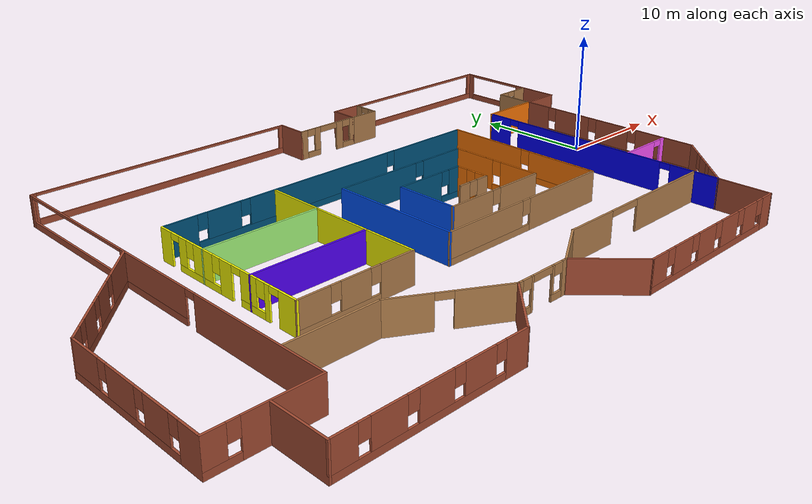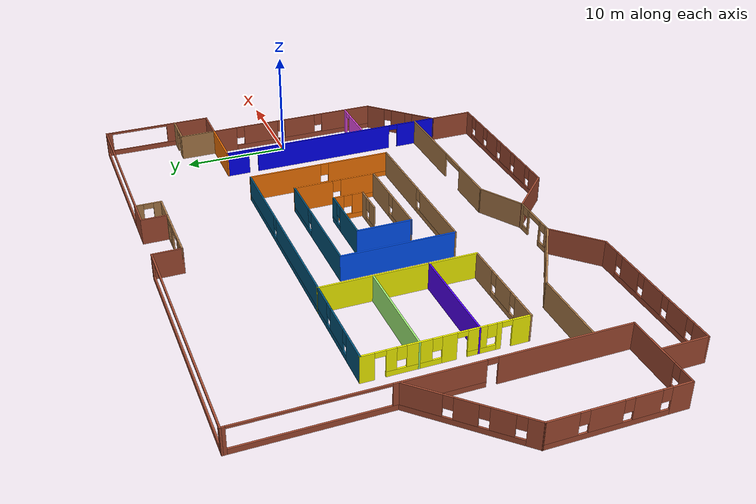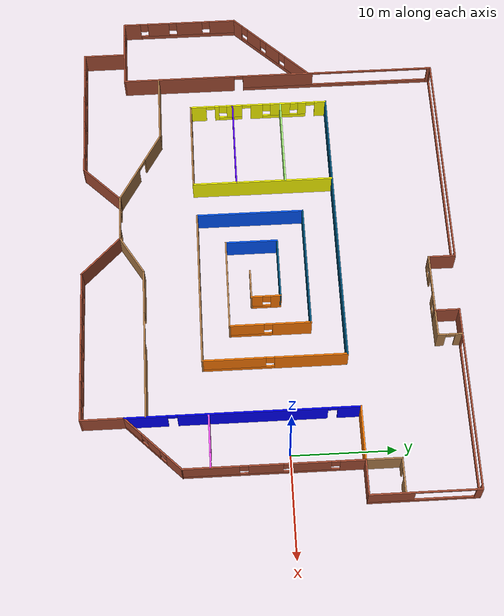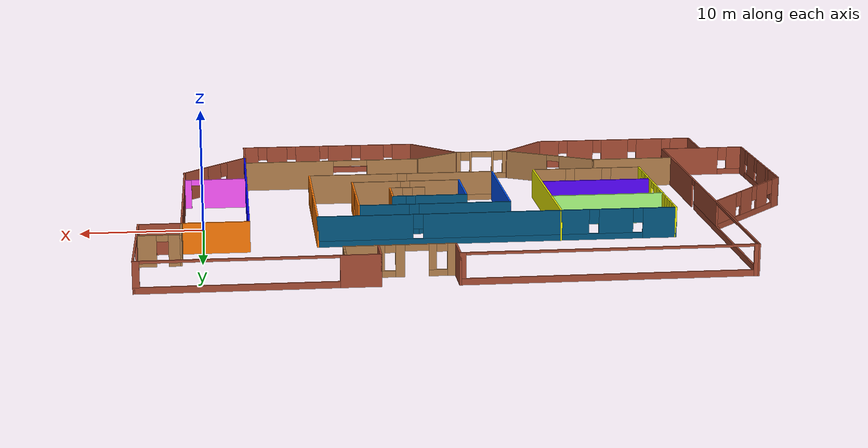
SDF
<?xml version='1.0'?>
<sdf version='1.6'>
  <model name='spiral_office'>
    <pose frame=''>-21.9737 -0.990625 0 0 -0 0</pose>
    <link name='Wall_10'>
      <pose frame=''>-8.28463 18.4006 0 0 -0 0</pose>
      <visual name='Wall_10_Visual_0'>
        <pose frame=''>-11.142 0 1.25 0 -0 0</pose>
        <geometry>
          <box>
            <size>0.465955 0.15 2.5</size>
          </box>
        </geometry>
        <material>
          <script>
            <uri>file://media/materials/scripts/gazebo.material</uri>
            <name>Gazebo/Bricks</name>
          </script>
          <ambient>1 1 1 1</ambient>
        </material>
        <meta>
          <layer>0</layer>
        </meta>
      </visual>
      <collision name='Wall_10_Collision_0'>
        <geometry>
          <box>
            <size>0.465955 0.15 2.5</size>
          </box>
        </geometry>
        <pose frame=''>-11.142 0 1.25 0 -0 0</pose>
      </collision>
      <visual name='Wall_10_Visual_1'>
        <pose frame=''>0.232978 0 0.25 0 -0 0</pose>
        <geometry>
          <box>
            <size>22.284 0.15 0.5</size>
          </box>
        </geometry>
        <material>
          <script>
            <uri>file://media/materials/scripts/gazebo.material</uri>
            <name>Gazebo/Bricks</name>
          </script>
          <ambient>1 1 1 1</ambient>
        </material>
        <meta>
          <layer>0</layer>
        </meta>
      </visual>
      <collision name='Wall_10_Collision_1'>
        <geometry>
          <box>
            <size>22.284 0.15 0.5</size>
          </box>
        </geometry>
        <pose frame=''>0.232978 0 0.25 0 -0 0</pose>
      </collision>
      <visual name='Wall_10_Visual_2'>
        <pose frame=''>11.1279 0 1.5 0 -0 0</pose>
        <geometry>
          <box>
            <size>0.494199 0.15 2</size>
          </box>
        </geometry>
        <material>
          <script>
            <uri>file://media/materials/scripts/gazebo.material</uri>
            <name>Gazebo/Bricks</name>
          </script>
          <ambient>1 1 1 1</ambient>
        </material>
        <meta>
          <layer>0</layer>
        </meta>
      </visual>
      <collision name='Wall_10_Collision_2'>
        <geometry>
          <box>
            <size>0.494199 0.15 2</size>
          </box>
        </geometry>
        <pose frame=''>11.1279 0 1.5 0 -0 0</pose>
      </collision>
      <visual name='Wall_10_Visual_3'>
        <pose frame=''>-0.014122 0 2.4 0 -0 0</pose>
        <geometry>
          <box>
            <size>21.7898 0.15 0.2</size>
          </box>
        </geometry>
        <material>
          <script>
            <uri>file://media/materials/scripts/gazebo.material</uri>
            <name>Gazebo/Bricks</name>
          </script>
          <ambient>1 1 1 1</ambient>
        </material>
        <meta>
          <layer>0</layer>
        </meta>
      </visual>
      <collision name='Wall_10_Collision_3'>
        <geometry>
          <box>
            <size>21.7898 0.15 0.2</size>
          </box>
        </geometry>
        <pose frame=''>-0.014122 0 2.4 0 -0 0</pose>
      </collision>
    </link>
    <link name='Wall_100'>
      <pose frame=''>20.9892 -6.43138 0 0 -0 3.14159</pose>
      <visual name='Wall_100_Visual_0'>
        <pose frame=''>-2.35489 0 1.25 0 -0 0</pose>
        <geometry>
          <box>
            <size>0.689225 0.15 2.5</size>
          </box>
        </geometry>
        <material>
          <script>
            <uri>file://media/materials/scripts/gazebo.material</uri>
            <name>Gazebo/Grey</name>
          </script>
          <ambient>1 0.333333 1 1</ambient>
        </material>
        <meta>
          <layer>0</layer>
        </meta>
      </visual>
      <collision name='Wall_100_Collision_0'>
        <geometry>
          <box>
            <size>0.689225 0.15 2.5</size>
          </box>
        </geometry>
        <pose frame=''>-2.35489 0 1.25 0 -0 0</pose>
      </collision>
      <visual name='Wall_100_Visual_1'>
        <pose frame=''>0.794612 0 1.25 0 -0 0</pose>
        <geometry>
          <box>
            <size>3.80978 0.15 2.5</size>
          </box>
        </geometry>
        <material>
          <script>
            <uri>file://media/materials/scripts/gazebo.material</uri>
            <name>Gazebo/Grey</name>
          </script>
          <ambient>1 0.333333 1 1</ambient>
        </material>
        <meta>
          <layer>0</layer>
        </meta>
      </visual>
      <collision name='Wall_100_Collision_1'>
        <geometry>
          <box>
            <size>3.80978 0.15 2.5</size>
          </box>
        </geometry>
        <pose frame=''>0.794612 0 1.25 0 -0 0</pose>
      </collision>
      <visual name='Wall_100_Visual_2'>
        <pose frame=''>-1.56028 0 2.25 0 -0 0</pose>
        <geometry>
          <box>
            <size>0.9 0.15 0.5</size>
          </box>
        </geometry>
        <material>
          <script>
            <uri>file://media/materials/scripts/gazebo.material</uri>
            <name>Gazebo/Grey</name>
          </script>
          <ambient>1 0.333333 1 1</ambient>
        </material>
        <meta>
          <layer>0</layer>
        </meta>
      </visual>
      <collision name='Wall_100_Collision_2'>
        <geometry>
          <box>
            <size>0.9 0.15 0.5</size>
          </box>
        </geometry>
        <pose frame=''>-1.56028 0 2.25 0 -0 0</pose>
      </collision>
    </link>
    <link name='Wall_102'>
      <pose frame=''>10.7001 -12.2894 0 0 -0 3.14159</pose>
      <visual name='Wall_102_Visual_0'>
        <pose frame=''>-3.79286 0 1.25 0 -0 0</pose>
        <geometry>
          <box>
            <size>7.82905 0.15 2.5</size>
          </box>
        </geometry>
        <material>
          <script>
            <uri>file://media/materials/scripts/gazebo.material</uri>
            <name>Gazebo/Wood</name>
          </script>
          <ambient>1 1 1 1</ambient>
        </material>
        <meta>
          <layer>0</layer>
        </meta>
      </visual>
      <collision name='Wall_102_Collision_0'>
        <geometry>
          <box>
            <size>7.82905 0.15 2.5</size>
          </box>
        </geometry>
        <pose frame=''>-3.79286 0 1.25 0 -0 0</pose>
      </collision>
      <visual name='Wall_102_Visual_1'>
        <pose frame=''>5.41453 0 1.25 0 -0 0</pose>
        <geometry>
          <box>
            <size>4.58572 0.15 2.5</size>
          </box>
        </geometry>
        <material>
          <script>
            <uri>file://media/materials/scripts/gazebo.material</uri>
            <name>Gazebo/Wood</name>
          </script>
          <ambient>1 1 1 1</ambient>
        </material>
        <meta>
          <layer>0</layer>
        </meta>
      </visual>
      <collision name='Wall_102_Collision_1'>
        <geometry>
          <box>
            <size>4.58572 0.15 2.5</size>
          </box>
        </geometry>
        <pose frame=''>5.41453 0 1.25 0 -0 0</pose>
      </collision>
      <visual name='Wall_102_Visual_2'>
        <pose frame=''>1.62166 0 2.25 0 -0 0</pose>
        <geometry>
          <box>
            <size>3 0.15 0.5</size>
          </box>
        </geometry>
        <material>
          <script>
            <uri>file://media/materials/scripts/gazebo.material</uri>
            <name>Gazebo/Wood</name>
          </script>
          <ambient>1 1 1 1</ambient>
        </material>
        <meta>
          <layer>0</layer>
        </meta>
      </visual>
      <collision name='Wall_102_Collision_2'>
        <geometry>
          <box>
            <size>3 0.15 0.5</size>
          </box>
        </geometry>
        <pose frame=''>1.62166 0 2.25 0 -0 0</pose>
      </collision>
    </link>
    <link name='Wall_103'>
      <collision name='Wall_103_Collision'>
        <geometry>
          <box>
            <size>4.56386 0.15 2.5</size>
          </box>
        </geometry>
        <pose frame=''>0 0 1.25 0 -0 0</pose>
      </collision>
      <visual name='Wall_103_Visual'>
        <pose frame=''>0 0 1.25 0 -0 0</pose>
        <geometry>
          <box>
            <size>4.56386 0.15 2.5</size>
          </box>
        </geometry>
        <material>
          <script>
            <uri>file://media/materials/scripts/gazebo.material</uri>
            <name>Gazebo/Wood</name>
          </script>
          <ambient>1 1 1 1</ambient>
        </material>
        <meta>
          <layer>0</layer>
        </meta>
      </visual>
      <pose frame=''>1.17619 -13.4264 0 0 0 -2.60036</pose>
    </link>
    <link name='Wall_11'>
      <collision name='Wall_11_Collision'>
        <geometry>
          <box>
            <size>2.75 0.15 2.5</size>
          </box>
        </geometry>
        <pose frame=''>0 0 1.25 0 -0 0</pose>
      </collision>
      <visual name='Wall_11_Visual'>
        <pose frame=''>0 0 1.25 0 -0 0</pose>
        <geometry>
          <box>
            <size>2.75 0.15 2.5</size>
          </box>
        </geometry>
        <material>
          <script>
            <uri>file://media/materials/scripts/gazebo.material</uri>
            <name>Gazebo/Bricks</name>
          </script>
          <ambient>1 1 1 1</ambient>
        </material>
        <meta>
          <layer>0</layer>
        </meta>
      </visual>
      <pose frame=''>3.01537 17.1006 0 0 0 -1.5708</pose>
    </link>
    <link name='Wall_12'>
      <pose frame=''>5.94037 15.8006 0 0 -0 0</pose>
      <visual name='Wall_12_Visual_0'>
        <pose frame=''>-2.63334 0 1.25 0 -0 0</pose>
        <geometry>
          <box>
            <size>0.733327 0.15 2.5</size>
          </box>
        </geometry>
        <material>
          <script>
            <uri>file://media/materials/scripts/gazebo.material</uri>
            <name>Gazebo/Wood</name>
          </script>
          <ambient>1 1 1 1</ambient>
        </material>
        <meta>
          <layer>0</layer>
        </meta>
      </visual>
      <collision name='Wall_12_Collision_0'>
        <geometry>
          <box>
            <size>0.733327 0.15 2.5</size>
          </box>
        </geometry>
        <pose frame=''>-2.63334 0 1.25 0 -0 0</pose>
      </collision>
      <visual name='Wall_12_Visual_1'>
        <pose frame=''>1.29307 0 1.25 0 -0 0</pose>
        <geometry>
          <box>
            <size>0.719491 0.15 2.5</size>
          </box>
        </geometry>
        <material>
          <script>
            <uri>file://media/materials/scripts/gazebo.material</uri>
            <name>Gazebo/Wood</name>
          </script>
          <ambient>1 1 1 1</ambient>
        </material>
        <meta>
          <layer>0</layer>
        </meta>
      </visual>
      <collision name='Wall_12_Collision_1'>
        <geometry>
          <box>
            <size>0.719491 0.15 2.5</size>
          </box>
        </geometry>
        <pose frame=''>1.29307 0 1.25 0 -0 0</pose>
      </collision>
      <visual name='Wall_12_Visual_2'>
        <pose frame=''>-1.56667 0 0.25 0 -0 0</pose>
        <geometry>
          <box>
            <size>1.4 0.15 0.5</size>
          </box>
        </geometry>
        <material>
          <script>
            <uri>file://media/materials/scripts/gazebo.material</uri>
            <name>Gazebo/Wood</name>
          </script>
          <ambient>1 1 1 1</ambient>
        </material>
        <meta>
          <layer>0</layer>
        </meta>
      </visual>
      <collision name='Wall_12_Collision_2'>
        <geometry>
          <box>
            <size>1.4 0.15 0.5</size>
          </box>
        </geometry>
        <pose frame=''>-1.56667 0 0.25 0 -0 0</pose>
      </collision>
      <visual name='Wall_12_Visual_3'>
        <pose frame=''>2.32641 0 0.25 0 -0 0</pose>
        <geometry>
          <box>
            <size>1.34718 0.15 0.5</size>
          </box>
        </geometry>
        <material>
          <script>
            <uri>file://media/materials/scripts/gazebo.material</uri>
            <name>Gazebo/Wood</name>
          </script>
          <ambient>1 1 1 1</ambient>
        </material>
        <meta>
          <layer>0</layer>
        </meta>
      </visual>
      <collision name='Wall_12_Collision_3'>
        <geometry>
          <box>
            <size>1.34718 0.15 0.5</size>
          </box>
        </geometry>
        <pose frame=''>2.32641 0 0.25 0 -0 0</pose>
      </collision>
      <visual name='Wall_12_Visual_4'>
        <pose frame=''>-1.16667 0 1.5 0 -0 0</pose>
        <geometry>
          <box>
            <size>0.6 0.15 2</size>
          </box>
        </geometry>
        <material>
          <script>
            <uri>file://media/materials/scripts/gazebo.material</uri>
            <name>Gazebo/Wood</name>
          </script>
          <ambient>1 1 1 1</ambient>
        </material>
        <meta>
          <layer>0</layer>
        </meta>
      </visual>
      <collision name='Wall_12_Collision_4'>
        <geometry>
          <box>
            <size>0.6 0.15 2</size>
          </box>
        </geometry>
        <pose frame=''>-1.16667 0 1.5 0 -0 0</pose>
      </collision>
      <visual name='Wall_12_Visual_5'>
        <pose frame=''>-1.16667 0 1.5 0 -0 0</pose>
        <geometry>
          <box>
            <size>0.6 0.15 2</size>
          </box>
        </geometry>
        <material>
          <script>
            <uri>file://media/materials/scripts/gazebo.material</uri>
            <name>Gazebo/Wood</name>
          </script>
          <ambient>1 1 1 1</ambient>
        </material>
        <meta>
          <layer>0</layer>
        </meta>
      </visual>
      <collision name='Wall_12_Collision_5'>
        <geometry>
          <box>
            <size>0.6 0.15 2</size>
          </box>
        </geometry>
        <pose frame=''>-1.16667 0 1.5 0 -0 0</pose>
      </collision>
      <visual name='Wall_12_Visual_6'>
        <pose frame=''>2.72641 0 1.5 0 -0 0</pose>
        <geometry>
          <box>
            <size>0.547182 0.15 2</size>
          </box>
        </geometry>
        <material>
          <script>
            <uri>file://media/materials/scripts/gazebo.material</uri>
            <name>Gazebo/Wood</name>
          </script>
          <ambient>1 1 1 1</ambient>
        </material>
        <meta>
          <layer>0</layer>
        </meta>
      </visual>
      <collision name='Wall_12_Collision_6'>
        <geometry>
          <box>
            <size>0.547182 0.15 2</size>
          </box>
        </geometry>
        <pose frame=''>2.72641 0 1.5 0 -0 0</pose>
      </collision>
      <visual name='Wall_12_Visual_7'>
        <pose frame=''>-1.86667 0 2.2 0 -0 0</pose>
        <geometry>
          <box>
            <size>0.8 0.15 0.6</size>
          </box>
        </geometry>
        <material>
          <script>
            <uri>file://media/materials/scripts/gazebo.material</uri>
            <name>Gazebo/Wood</name>
          </script>
          <ambient>1 1 1 1</ambient>
        </material>
        <meta>
          <layer>0</layer>
        </meta>
      </visual>
      <collision name='Wall_12_Collision_7'>
        <geometry>
          <box>
            <size>0.8 0.15 0.6</size>
          </box>
        </geometry>
        <pose frame=''>-1.86667 0 2.2 0 -0 0</pose>
      </collision>
      <visual name='Wall_12_Visual_8'>
        <pose frame=''>2.05282 0 2.2 0 -0 0</pose>
        <geometry>
          <box>
            <size>0.8 0.15 0.6</size>
          </box>
        </geometry>
        <material>
          <script>
            <uri>file://media/materials/scripts/gazebo.material</uri>
            <name>Gazebo/Wood</name>
          </script>
          <ambient>1 1 1 1</ambient>
        </material>
        <meta>
          <layer>0</layer>
        </meta>
      </visual>
      <collision name='Wall_12_Collision_8'>
        <geometry>
          <box>
            <size>0.8 0.15 0.6</size>
          </box>
        </geometry>
        <pose frame=''>2.05282 0 2.2 0 -0 0</pose>
      </collision>
      <visual name='Wall_12_Visual_9'>
        <pose frame=''>0.033327 0 2.25 0 -0 0</pose>
        <geometry>
          <box>
            <size>1.8 0.15 0.5</size>
          </box>
        </geometry>
        <material>
          <script>
            <uri>file://media/materials/scripts/gazebo.material</uri>
            <name>Gazebo/Wood</name>
          </script>
          <ambient>1 1 1 1</ambient>
        </material>
        <meta>
          <layer>0</layer>
        </meta>
      </visual>
      <collision name='Wall_12_Collision_9'>
        <geometry>
          <box>
            <size>1.8 0.15 0.5</size>
          </box>
        </geometry>
        <pose frame=''>0.033327 0 2.25 0 -0 0</pose>
      </collision>
      <visual name='Wall_12_Visual_10'>
        <pose frame=''>0.033327 0 2.25 0 -0 0</pose>
        <geometry>
          <box>
            <size>1.8 0.15 0.5</size>
          </box>
        </geometry>
        <material>
          <script>
            <uri>file://media/materials/scripts/gazebo.material</uri>
            <name>Gazebo/Wood</name>
          </script>
          <ambient>1 1 1 1</ambient>
        </material>
        <meta>
          <layer>0</layer>
        </meta>
      </visual>
      <collision name='Wall_12_Collision_10'>
        <geometry>
          <box>
            <size>1.8 0.15 0.5</size>
          </box>
        </geometry>
        <pose frame=''>0.033327 0 2.25 0 -0 0</pose>
      </collision>
    </link>
    <link name='Wall_13'>
      <collision name='Wall_13_Collision'>
        <geometry>
          <box>
            <size>2.5 0.15 2.5</size>
          </box>
        </geometry>
        <pose frame=''>0 0 1.25 0 -0 0</pose>
      </collision>
      <visual name='Wall_13_Visual'>
        <pose frame=''>0 0 1.25 0 -0 0</pose>
        <geometry>
          <box>
            <size>2.5 0.15 2.5</size>
          </box>
        </geometry>
        <material>
          <script>
            <uri>file://media/materials/scripts/gazebo.material</uri>
            <name>Gazebo/Bricks</name>
          </script>
          <ambient>1 1 1 1</ambient>
        </material>
        <meta>
          <layer>0</layer>
        </meta>
      </visual>
      <pose frame=''>8.86537 16.9756 0 0 -0 1.5708</pose>
    </link>
    <link name='Wall_14'>
      <pose frame=''>17.9154 18.1506 0 0 -0 0</pose>
      <visual name='Wall_14_Visual_0'>
        <pose frame=''>-7.57768 0 1.25 0 -0 0</pose>
        <geometry>
          <box>
            <size>3.09465 0.15 2.5</size>
          </box>
        </geometry>
        <material>
          <script>
            <uri>file://media/materials/scripts/gazebo.material</uri>
            <name>Gazebo/Bricks</name>
          </script>
          <ambient>1 1 1 1</ambient>
        </material>
        <meta>
          <layer>0</layer>
        </meta>
      </visual>
      <collision name='Wall_14_Collision_0'>
        <geometry>
          <box>
            <size>3.09465 0.15 2.5</size>
          </box>
        </geometry>
        <pose frame=''>-7.57768 0 1.25 0 -0 0</pose>
      </collision>
      <visual name='Wall_14_Visual_1'>
        <pose frame=''>1.54732 0 0.25 0 -0 0</pose>
        <geometry>
          <box>
            <size>15.1554 0.15 0.5</size>
          </box>
        </geometry>
        <material>
          <script>
            <uri>file://media/materials/scripts/gazebo.material</uri>
            <name>Gazebo/Bricks</name>
          </script>
          <ambient>1 1 1 1</ambient>
        </material>
        <meta>
          <layer>0</layer>
        </meta>
      </visual>
      <collision name='Wall_14_Collision_1'>
        <geometry>
          <box>
            <size>15.1554 0.15 0.5</size>
          </box>
        </geometry>
        <pose frame=''>1.54732 0 0.25 0 -0 0</pose>
      </collision>
      <visual name='Wall_14_Visual_2'>
        <pose frame=''>8.85582 0 1.5 0 -0 0</pose>
        <geometry>
          <box>
            <size>0.538352 0.15 2</size>
          </box>
        </geometry>
        <material>
          <script>
            <uri>file://media/materials/scripts/gazebo.material</uri>
            <name>Gazebo/Bricks</name>
          </script>
          <ambient>1 1 1 1</ambient>
        </material>
        <meta>
          <layer>0</layer>
        </meta>
      </visual>
      <collision name='Wall_14_Collision_2'>
        <geometry>
          <box>
            <size>0.538352 0.15 2</size>
          </box>
        </geometry>
        <pose frame=''>8.85582 0 1.5 0 -0 0</pose>
      </collision>
      <visual name='Wall_14_Visual_3'>
        <pose frame=''>1.27815 0 2.4 0 -0 0</pose>
        <geometry>
          <box>
            <size>14.617 0.15 0.2</size>
          </box>
        </geometry>
        <material>
          <script>
            <uri>file://media/materials/scripts/gazebo.material</uri>
            <name>Gazebo/Bricks</name>
          </script>
          <ambient>1 1 1 1</ambient>
        </material>
        <meta>
          <layer>0</layer>
        </meta>
      </visual>
      <collision name='Wall_14_Collision_3'>
        <geometry>
          <box>
            <size>14.617 0.15 0.2</size>
          </box>
        </geometry>
        <pose frame=''>1.27815 0 2.4 0 -0 0</pose>
      </collision>
    </link>
    <link name='Wall_15'>
      <pose frame=''>26.9654 12.9756 0 0 0 -1.5708</pose>
      <visual name='Wall_15_Visual_0'>
        <pose frame=''>-4.93489 0 1.25 0 -0 0</pose>
        <geometry>
          <box>
            <size>0.630216 0.15 2.5</size>
          </box>
        </geometry>
        <material>
          <script>
            <uri>file://media/materials/scripts/gazebo.material</uri>
            <name>Gazebo/Bricks</name>
          </script>
          <ambient>1 1 1 1</ambient>
        </material>
        <meta>
          <layer>0</layer>
        </meta>
      </visual>
      <collision name='Wall_15_Collision_0'>
        <geometry>
          <box>
            <size>0.630216 0.15 2.5</size>
          </box>
        </geometry>
        <pose frame=''>-4.93489 0 1.25 0 -0 0</pose>
      </collision>
      <visual name='Wall_15_Visual_1'>
        <pose frame=''>0.315108 0 0.25 0 -0 0</pose>
        <geometry>
          <box>
            <size>9.86978 0.15 0.5</size>
          </box>
        </geometry>
        <material>
          <script>
            <uri>file://media/materials/scripts/gazebo.material</uri>
            <name>Gazebo/Bricks</name>
          </script>
          <ambient>1 1 1 1</ambient>
        </material>
        <meta>
          <layer>0</layer>
        </meta>
      </visual>
      <collision name='Wall_15_Collision_1'>
        <geometry>
          <box>
            <size>9.86978 0.15 0.5</size>
          </box>
        </geometry>
        <pose frame=''>0.315108 0 0.25 0 -0 0</pose>
      </collision>
      <visual name='Wall_15_Visual_2'>
        <pose frame=''>3.09761 0 1.5 0 -0 0</pose>
        <geometry>
          <box>
            <size>4.30478 0.15 2</size>
          </box>
        </geometry>
        <material>
          <script>
            <uri>file://media/materials/scripts/gazebo.material</uri>
            <name>Gazebo/Bricks</name>
          </script>
          <ambient>1 1 1 1</ambient>
        </material>
        <meta>
          <layer>0</layer>
        </meta>
      </visual>
      <collision name='Wall_15_Collision_2'>
        <geometry>
          <box>
            <size>4.30478 0.15 2</size>
          </box>
        </geometry>
        <pose frame=''>3.09761 0 1.5 0 -0 0</pose>
      </collision>
      <visual name='Wall_15_Visual_3'>
        <pose frame=''>-1.83728 0 2.4 0 -0 0</pose>
        <geometry>
          <box>
            <size>5.565 0.15 0.2</size>
          </box>
        </geometry>
        <material>
          <script>
            <uri>file://media/materials/scripts/gazebo.material</uri>
            <name>Gazebo/Bricks</name>
          </script>
          <ambient>1 1 1 1</ambient>
        </material>
        <meta>
          <layer>0</layer>
        </meta>
      </visual>
      <collision name='Wall_15_Collision_3'>
        <geometry>
          <box>
            <size>5.565 0.15 0.2</size>
          </box>
        </geometry>
        <pose frame=''>-1.83728 0 2.4 0 -0 0</pose>
      </collision>
    </link>
    <link name='Wall_16'>
      <collision name='Wall_16_Collision'>
        <geometry>
          <box>
            <size>3.50167 0.15 2.5</size>
          </box>
        </geometry>
        <pose frame=''>0 0 1.25 0 -0 0</pose>
      </collision>
      <visual name='Wall_16_Visual'>
        <pose frame=''>0 0 1.25 0 -0 0</pose>
        <geometry>
          <box>
            <size>3.50167 0.15 2.5</size>
          </box>
        </geometry>
        <material>
          <script>
            <uri>file://media/materials/scripts/gazebo.material</uri>
            <name>Gazebo/Bricks</name>
          </script>
          <ambient>1 1 1 1</ambient>
        </material>
        <meta>
          <layer>0</layer>
        </meta>
      </visual>
      <pose frame=''>25.2895 7.80063 0 0 0 -3.14159</pose>
    </link>
    <link name='Wall_17'>
      <pose frame=''>23.6145 -0.624368 0 0 0 -1.5707</pose>
      <visual name='Wall_17_Visual_0'>
        <pose frame=''>-7.2888 0 1.25 0 -0 0</pose>
        <geometry>
          <box>
            <size>2.42239 0.15 2.5</size>
          </box>
        </geometry>
        <material>
          <script>
            <uri>file://media/materials/scripts/gazebo.material</uri>
            <name>Gazebo/Bricks</name>
          </script>
          <ambient>1 1 1 1</ambient>
        </material>
        <meta>
          <layer>0</layer>
        </meta>
      </visual>
      <collision name='Wall_17_Collision_0'>
        <geometry>
          <box>
            <size>2.42239 0.15 2.5</size>
          </box>
        </geometry>
        <pose frame=''>-7.2888 0 1.25 0 -0 0</pose>
      </collision>
      <visual name='Wall_17_Visual_1'>
        <pose frame=''>1.2112 0 0.25 0 -0 0</pose>
        <geometry>
          <box>
            <size>14.5776 0.15 0.5</size>
          </box>
        </geometry>
        <material>
          <script>
            <uri>file://media/materials/scripts/gazebo.material</uri>
            <name>Gazebo/Bricks</name>
          </script>
          <ambient>1 1 1 1</ambient>
        </material>
        <meta>
          <layer>0</layer>
        </meta>
      </visual>
      <collision name='Wall_17_Collision_1'>
        <geometry>
          <box>
            <size>14.5776 0.15 0.5</size>
          </box>
        </geometry>
        <pose frame=''>1.2112 0 0.25 0 -0 0</pose>
      </collision>
      <visual name='Wall_17_Visual_2'>
        <pose frame=''>-3.48164 0 1.5 0 -0 0</pose>
        <geometry>
          <box>
            <size>3.59193 0.15 2</size>
          </box>
        </geometry>
        <material>
          <script>
            <uri>file://media/materials/scripts/gazebo.material</uri>
            <name>Gazebo/Bricks</name>
          </script>
          <ambient>1 1 1 1</ambient>
        </material>
        <meta>
          <layer>0</layer>
        </meta>
      </visual>
      <collision name='Wall_17_Collision_2'>
        <geometry>
          <box>
            <size>3.59193 0.15 2</size>
          </box>
        </geometry>
        <pose frame=''>-3.48164 0 1.5 0 -0 0</pose>
      </collision>
      <visual name='Wall_17_Visual_3'>
        <pose frame=''>0.737324 0 1.5 0 -0 0</pose>
        <geometry>
          <box>
            <size>3.246 0.15 2</size>
          </box>
        </geometry>
        <material>
          <script>
            <uri>file://media/materials/scripts/gazebo.material</uri>
            <name>Gazebo/Bricks</name>
          </script>
          <ambient>1 1 1 1</ambient>
        </material>
        <meta>
          <layer>0</layer>
        </meta>
      </visual>
      <collision name='Wall_17_Collision_3'>
        <geometry>
          <box>
            <size>3.246 0.15 2</size>
          </box>
        </geometry>
        <pose frame=''>0.737324 0 1.5 0 -0 0</pose>
      </collision>
      <visual name='Wall_17_Visual_4'>
        <pose frame=''>5.83016 0 1.5 0 -0 0</pose>
        <geometry>
          <box>
            <size>5.33968 0.15 2</size>
          </box>
        </geometry>
        <material>
          <script>
            <uri>file://media/materials/scripts/gazebo.material</uri>
            <name>Gazebo/Bricks</name>
          </script>
          <ambient>1 1 1 1</ambient>
        </material>
        <meta>
          <layer>0</layer>
        </meta>
      </visual>
      <collision name='Wall_17_Collision_4'>
        <geometry>
          <box>
            <size>5.33968 0.15 2</size>
          </box>
        </geometry>
        <pose frame=''>5.83016 0 1.5 0 -0 0</pose>
      </collision>
      <visual name='Wall_17_Visual_5'>
        <pose frame=''>-5.67761 0 1.9 0 -0 0</pose>
        <geometry>
          <box>
            <size>0.8 0.15 1.2</size>
          </box>
        </geometry>
        <material>
          <script>
            <uri>file://media/materials/scripts/gazebo.material</uri>
            <name>Gazebo/Bricks</name>
          </script>
          <ambient>1 1 1 1</ambient>
        </material>
        <meta>
          <layer>0</layer>
        </meta>
      </visual>
      <collision name='Wall_17_Collision_5'>
        <geometry>
          <box>
            <size>0.8 0.15 1.2</size>
          </box>
        </geometry>
        <pose frame=''>-5.67761 0 1.9 0 -0 0</pose>
      </collision>
      <visual name='Wall_17_Visual_6'>
        <pose frame=''>-1.28568 0 1.9 0 -0 0</pose>
        <geometry>
          <box>
            <size>0.8 0.15 1.2</size>
          </box>
        </geometry>
        <material>
          <script>
            <uri>file://media/materials/scripts/gazebo.material</uri>
            <name>Gazebo/Bricks</name>
          </script>
          <ambient>1 1 1 1</ambient>
        </material>
        <meta>
          <layer>0</layer>
        </meta>
      </visual>
      <collision name='Wall_17_Collision_6'>
        <geometry>
          <box>
            <size>0.8 0.15 1.2</size>
          </box>
        </geometry>
        <pose frame=''>-1.28568 0 1.9 0 -0 0</pose>
      </collision>
      <visual name='Wall_17_Visual_7'>
        <pose frame=''>2.76032 0 1.9 0 -0 0</pose>
        <geometry>
          <box>
            <size>0.8 0.15 1.2</size>
          </box>
        </geometry>
        <material>
          <script>
            <uri>file://media/materials/scripts/gazebo.material</uri>
            <name>Gazebo/Bricks</name>
          </script>
          <ambient>1 1 1 1</ambient>
        </material>
        <meta>
          <layer>0</layer>
        </meta>
      </visual>
      <collision name='Wall_17_Collision_7'>
        <geometry>
          <box>
            <size>0.8 0.15 1.2</size>
          </box>
        </geometry>
        <pose frame=''>2.76032 0 1.9 0 -0 0</pose>
      </collision>
    </link>
    <link name='Wall_18'>
      <pose frame=''>20.99 -11.6749 0 0 0 -2.35616</pose>
      <visual name='Wall_18_Visual_0'>
        <pose frame=''>-2.76411 0 1.25 0 -0 0</pose>
        <geometry>
          <box>
            <size>2.04759 0.15 2.5</size>
          </box>
        </geometry>
        <material>
          <script>
            <uri>file://media/materials/scripts/gazebo.material</uri>
            <name>Gazebo/Bricks</name>
          </script>
          <ambient>1 1 1 1</ambient>
        </material>
        <meta>
          <layer>0</layer>
        </meta>
      </visual>
      <collision name='Wall_18_Collision_0'>
        <geometry>
          <box>
            <size>2.04759 0.15 2.5</size>
          </box>
        </geometry>
        <pose frame=''>-2.76411 0 1.25 0 -0 0</pose>
      </collision>
      <visual name='Wall_18_Visual_1'>
        <pose frame=''>1.02379 0 0.25 0 -0 0</pose>
        <geometry>
          <box>
            <size>5.52823 0.15 0.5</size>
          </box>
        </geometry>
        <material>
          <script>
            <uri>file://media/materials/scripts/gazebo.material</uri>
            <name>Gazebo/Bricks</name>
          </script>
          <ambient>1 1 1 1</ambient>
        </material>
        <meta>
          <layer>0</layer>
        </meta>
      </visual>
      <collision name='Wall_18_Collision_1'>
        <geometry>
          <box>
            <size>5.52823 0.15 0.5</size>
          </box>
        </geometry>
        <pose frame=''>1.02379 0 0.25 0 -0 0</pose>
      </collision>
      <visual name='Wall_18_Visual_2'>
        <pose frame=''>-0.167532 0 1.5 0 -0 0</pose>
        <geometry>
          <box>
            <size>1.54558 0.15 2</size>
          </box>
        </geometry>
        <material>
          <script>
            <uri>file://media/materials/scripts/gazebo.material</uri>
            <name>Gazebo/Bricks</name>
          </script>
          <ambient>1 1 1 1</ambient>
        </material>
        <meta>
          <layer>0</layer>
        </meta>
      </visual>
      <collision name='Wall_18_Collision_2'>
        <geometry>
          <box>
            <size>1.54558 0.15 2</size>
          </box>
        </geometry>
        <pose frame=''>-0.167532 0 1.5 0 -0 0</pose>
      </collision>
      <visual name='Wall_18_Visual_3'>
        <pose frame=''>2.59658 0 1.5 0 -0 0</pose>
        <geometry>
          <box>
            <size>2.38265 0.15 2</size>
          </box>
        </geometry>
        <material>
          <script>
            <uri>file://media/materials/scripts/gazebo.material</uri>
            <name>Gazebo/Bricks</name>
          </script>
          <ambient>1 1 1 1</ambient>
        </material>
        <meta>
          <layer>0</layer>
        </meta>
      </visual>
      <collision name='Wall_18_Collision_3'>
        <geometry>
          <box>
            <size>2.38265 0.15 2</size>
          </box>
        </geometry>
        <pose frame=''>2.59658 0 1.5 0 -0 0</pose>
      </collision>
      <visual name='Wall_18_Visual_4'>
        <pose frame=''>-1.34032 0 1.9 0 -0 0</pose>
        <geometry>
          <box>
            <size>0.8 0.15 1.2</size>
          </box>
        </geometry>
        <material>
          <script>
            <uri>file://media/materials/scripts/gazebo.material</uri>
            <name>Gazebo/Bricks</name>
          </script>
          <ambient>1 1 1 1</ambient>
        </material>
        <meta>
          <layer>0</layer>
        </meta>
      </visual>
      <collision name='Wall_18_Collision_4'>
        <geometry>
          <box>
            <size>0.8 0.15 1.2</size>
          </box>
        </geometry>
        <pose frame=''>-1.34032 0 1.9 0 -0 0</pose>
      </collision>
      <visual name='Wall_18_Visual_5'>
        <pose frame=''>1.00526 0 1.9 0 -0 0</pose>
        <geometry>
          <box>
            <size>0.8 0.15 1.2</size>
          </box>
        </geometry>
        <material>
          <script>
            <uri>file://media/materials/scripts/gazebo.material</uri>
            <name>Gazebo/Bricks</name>
          </script>
          <ambient>1 1 1 1</ambient>
        </material>
        <meta>
          <layer>0</layer>
        </meta>
      </visual>
      <collision name='Wall_18_Collision_5'>
        <geometry>
          <box>
            <size>0.8 0.15 1.2</size>
          </box>
        </geometry>
        <pose frame=''>1.00526 0 1.9 0 -0 0</pose>
      </collision>
    </link>
    <link name='Wall_19'>
      <collision name='Wall_19_Collision'>
        <geometry>
          <box>
            <size>4.25 0.15 2.5</size>
          </box>
        </geometry>
        <pose frame=''>0 0 1.25 0 -0 0</pose>
      </collision>
      <visual name='Wall_19_Visual'>
        <pose frame=''>0 0 1.25 0 -0 0</pose>
        <geometry>
          <box>
            <size>4.25 0.15 2.5</size>
          </box>
        </geometry>
        <material>
          <script>
            <uri>file://media/materials/scripts/gazebo.material</uri>
            <name>Gazebo/Bricks</name>
          </script>
          <ambient>1 1 1 1</ambient>
        </material>
        <meta>
          <layer>0</layer>
        </meta>
      </visual>
      <pose frame=''>18.3647 -16.3504 0 0 0 -1.5708</pose>
    </link>
    <link name='Wall_20'>
      <pose frame=''>10.7162 -18.3734 0 0 -0 3.13806</pose>
      <visual name='Wall_20_Visual_0'>
        <pose frame=''>-7.04407 0 1.25 0 -0 0</pose>
        <geometry>
          <box>
            <size>1.35851 0.15 2.5</size>
          </box>
        </geometry>
        <material>
          <script>
            <uri>file://media/materials/scripts/gazebo.material</uri>
            <name>Gazebo/Bricks</name>
          </script>
          <ambient>1 1 1 1</ambient>
        </material>
        <meta>
          <layer>0</layer>
        </meta>
      </visual>
      <collision name='Wall_20_Collision_0'>
        <geometry>
          <box>
            <size>1.35851 0.15 2.5</size>
          </box>
        </geometry>
        <pose frame=''>-7.04407 0 1.25 0 -0 0</pose>
      </collision>
      <visual name='Wall_20_Visual_1'>
        <pose frame=''>0.679257 0 0.25 0 -0 0</pose>
        <geometry>
          <box>
            <size>14.0881 0.15 0.5</size>
          </box>
        </geometry>
        <material>
          <script>
            <uri>file://media/materials/scripts/gazebo.material</uri>
            <name>Gazebo/Bricks</name>
          </script>
          <ambient>1 1 1 1</ambient>
        </material>
        <meta>
          <layer>0</layer>
        </meta>
      </visual>
      <collision name='Wall_20_Collision_1'>
        <geometry>
          <box>
            <size>14.0881 0.15 0.5</size>
          </box>
        </geometry>
        <pose frame=''>0.679257 0 0.25 0 -0 0</pose>
      </collision>
      <visual name='Wall_20_Visual_2'>
        <pose frame=''>-4.65396 0 1.5 0 -0 0</pose>
        <geometry>
          <box>
            <size>1.8217 0.15 2</size>
          </box>
        </geometry>
        <material>
          <script>
            <uri>file://media/materials/scripts/gazebo.material</uri>
            <name>Gazebo/Bricks</name>
          </script>
          <ambient>1 1 1 1</ambient>
        </material>
        <meta>
          <layer>0</layer>
        </meta>
      </visual>
      <collision name='Wall_20_Collision_2'>
        <geometry>
          <box>
            <size>1.8217 0.15 2</size>
          </box>
        </geometry>
        <pose frame=''>-4.65396 0 1.5 0 -0 0</pose>
      </collision>
      <visual name='Wall_20_Visual_3'>
        <pose frame=''>-1.84491 0 1.5 0 -0 0</pose>
        <geometry>
          <box>
            <size>2.19639 0.15 2</size>
          </box>
        </geometry>
        <material>
          <script>
            <uri>file://media/materials/scripts/gazebo.material</uri>
            <name>Gazebo/Bricks</name>
          </script>
          <ambient>1 1 1 1</ambient>
        </material>
        <meta>
          <layer>0</layer>
        </meta>
      </visual>
      <collision name='Wall_20_Collision_3'>
        <geometry>
          <box>
            <size>2.19639 0.15 2</size>
          </box>
        </geometry>
        <pose frame=''>-1.84491 0 1.5 0 -0 0</pose>
      </collision>
      <visual name='Wall_20_Visual_4'>
        <pose frame=''>1.12473 0 1.5 0 -0 0</pose>
        <geometry>
          <box>
            <size>2.14289 0.15 2</size>
          </box>
        </geometry>
        <material>
          <script>
            <uri>file://media/materials/scripts/gazebo.material</uri>
            <name>Gazebo/Bricks</name>
          </script>
          <ambient>1 1 1 1</ambient>
        </material>
        <meta>
          <layer>0</layer>
        </meta>
      </visual>
      <collision name='Wall_20_Collision_4'>
        <geometry>
          <box>
            <size>2.14289 0.15 2</size>
          </box>
        </geometry>
        <pose frame=''>1.12473 0 1.5 0 -0 0</pose>
      </collision>
      <visual name='Wall_20_Visual_5'>
        <pose frame=''>4.06762 0 1.5 0 -0 0</pose>
        <geometry>
          <box>
            <size>2.14289 0.15 2</size>
          </box>
        </geometry>
        <material>
          <script>
            <uri>file://media/materials/scripts/gazebo.material</uri>
            <name>Gazebo/Bricks</name>
          </script>
          <ambient>1 1 1 1</ambient>
        </material>
        <meta>
          <layer>0</layer>
        </meta>
      </visual>
      <collision name='Wall_20_Collision_5'>
        <geometry>
          <box>
            <size>2.14289 0.15 2</size>
          </box>
        </geometry>
        <pose frame=''>4.06762 0 1.5 0 -0 0</pose>
      </collision>
      <visual name='Wall_20_Visual_6'>
        <pose frame=''>6.8312 0 1.5 0 -0 0</pose>
        <geometry>
          <box>
            <size>1.78426 0.15 2</size>
          </box>
        </geometry>
        <material>
          <script>
            <uri>file://media/materials/scripts/gazebo.material</uri>
            <name>Gazebo/Bricks</name>
          </script>
          <ambient>1 1 1 1</ambient>
        </material>
        <meta>
          <layer>0</layer>
        </meta>
      </visual>
      <collision name='Wall_20_Collision_6'>
        <geometry>
          <box>
            <size>1.78426 0.15 2</size>
          </box>
        </geometry>
        <pose frame=''>6.8312 0 1.5 0 -0 0</pose>
      </collision>
      <visual name='Wall_20_Visual_7'>
        <pose frame=''>-5.96481 0 1.9 0 -0 0</pose>
        <geometry>
          <box>
            <size>0.8 0.15 1.2</size>
          </box>
        </geometry>
        <material>
          <script>
            <uri>file://media/materials/scripts/gazebo.material</uri>
            <name>Gazebo/Bricks</name>
          </script>
          <ambient>1 1 1 1</ambient>
        </material>
        <meta>
          <layer>0</layer>
        </meta>
      </visual>
      <collision name='Wall_20_Collision_7'>
        <geometry>
          <box>
            <size>0.8 0.15 1.2</size>
          </box>
        </geometry>
        <pose frame=''>-5.96481 0 1.9 0 -0 0</pose>
      </collision>
      <visual name='Wall_20_Visual_8'>
        <pose frame=''>-3.34311 0 1.9 0 -0 0</pose>
        <geometry>
          <box>
            <size>0.8 0.15 1.2</size>
          </box>
        </geometry>
        <material>
          <script>
            <uri>file://media/materials/scripts/gazebo.material</uri>
            <name>Gazebo/Bricks</name>
          </script>
          <ambient>1 1 1 1</ambient>
        </material>
        <meta>
          <layer>0</layer>
        </meta>
      </visual>
      <collision name='Wall_20_Collision_8'>
        <geometry>
          <box>
            <size>0.8 0.15 1.2</size>
          </box>
        </geometry>
        <pose frame=''>-3.34311 0 1.9 0 -0 0</pose>
      </collision>
      <visual name='Wall_20_Visual_9'>
        <pose frame=''>-0.346715 0 1.9 0 -0 0</pose>
        <geometry>
          <box>
            <size>0.8 0.15 1.2</size>
          </box>
        </geometry>
        <material>
          <script>
            <uri>file://media/materials/scripts/gazebo.material</uri>
            <name>Gazebo/Bricks</name>
          </script>
          <ambient>1 1 1 1</ambient>
        </material>
        <meta>
          <layer>0</layer>
        </meta>
      </visual>
      <collision name='Wall_20_Collision_9'>
        <geometry>
          <box>
            <size>0.8 0.15 1.2</size>
          </box>
        </geometry>
        <pose frame=''>-0.346715 0 1.9 0 -0 0</pose>
      </collision>
      <visual name='Wall_20_Visual_10'>
        <pose frame=''>2.59618 0 1.9 0 -0 0</pose>
        <geometry>
          <box>
            <size>0.8 0.15 1.2</size>
          </box>
        </geometry>
        <material>
          <script>
            <uri>file://media/materials/scripts/gazebo.material</uri>
            <name>Gazebo/Bricks</name>
          </script>
          <ambient>1 1 1 1</ambient>
        </material>
        <meta>
          <layer>0</layer>
        </meta>
      </visual>
      <collision name='Wall_20_Collision_10'>
        <geometry>
          <box>
            <size>0.8 0.15 1.2</size>
          </box>
        </geometry>
        <pose frame=''>2.59618 0 1.9 0 -0 0</pose>
      </collision>
      <visual name='Wall_20_Visual_11'>
        <pose frame=''>5.53907 0 1.9 0 -0 0</pose>
        <geometry>
          <box>
            <size>0.8 0.15 1.2</size>
          </box>
        </geometry>
        <material>
          <script>
            <uri>file://media/materials/scripts/gazebo.material</uri>
            <name>Gazebo/Bricks</name>
          </script>
          <ambient>1 1 1 1</ambient>
        </material>
        <meta>
          <layer>0</layer>
        </meta>
      </visual>
      <collision name='Wall_20_Collision_11'>
        <geometry>
          <box>
            <size>0.8 0.15 1.2</size>
          </box>
        </geometry>
        <pose frame=''>5.53907 0 1.9 0 -0 0</pose>
      </collision>
    </link>
    <link name='Wall_21'>
      <collision name='Wall_21_Collision'>
        <geometry>
          <box>
            <size>5.5 0.15 2.5</size>
          </box>
        </geometry>
        <pose frame=''>0 0 1.25 0 -0 0</pose>
      </collision>
      <visual name='Wall_21_Visual'>
        <pose frame=''>0 0 1.25 0 -0 0</pose>
        <geometry>
          <box>
            <size>5.5 0.15 2.5</size>
          </box>
        </geometry>
        <material>
          <script>
            <uri>file://media/materials/scripts/gazebo.material</uri>
            <name>Gazebo/Bricks</name>
          </script>
          <ambient>1 1 1 1</ambient>
        </material>
        <meta>
          <layer>0</layer>
        </meta>
      </visual>
      <pose frame=''>1.17619 -16.4549 0 0 -0 2.35619</pose>
    </link>
    <link name='Wall_22'>
      <pose frame=''>-3.0151 -14.5635 0 0 0 -3.14155</pose>
      <visual name='Wall_22_Visual_0'>
        <pose frame=''>-2.1319 0 1.25 0 -0 0</pose>
        <geometry>
          <box>
            <size>0.486208 0.15 2.5</size>
          </box>
        </geometry>
        <material>
          <script>
            <uri>file://media/materials/scripts/gazebo.material</uri>
            <name>Gazebo/Wood</name>
          </script>
          <ambient>1 1 1 1</ambient>
        </material>
        <meta>
          <layer>0</layer>
        </meta>
      </visual>
      <collision name='Wall_22_Collision_0'>
        <geometry>
          <box>
            <size>0.486208 0.15 2.5</size>
          </box>
        </geometry>
        <pose frame=''>-2.1319 0 1.25 0 -0 0</pose>
      </collision>
      <visual name='Wall_22_Visual_1'>
        <pose frame=''>1.01121 0 1.25 0 -0 0</pose>
        <geometry>
          <box>
            <size>0.2 0.15 2.5</size>
          </box>
        </geometry>
        <material>
          <script>
            <uri>file://media/materials/scripts/gazebo.material</uri>
            <name>Gazebo/Wood</name>
          </script>
          <ambient>1 1 1 1</ambient>
        </material>
        <meta>
          <layer>0</layer>
        </meta>
      </visual>
      <collision name='Wall_22_Collision_1'>
        <geometry>
          <box>
            <size>0.2 0.15 2.5</size>
          </box>
        </geometry>
        <pose frame=''>1.01121 0 1.25 0 -0 0</pose>
      </collision>
      <visual name='Wall_22_Visual_2'>
        <pose frame=''>-1.38879 0 0.25 0 -0 0</pose>
        <geometry>
          <box>
            <size>1 0.15 0.5</size>
          </box>
        </geometry>
        <material>
          <script>
            <uri>file://media/materials/scripts/gazebo.material</uri>
            <name>Gazebo/Wood</name>
          </script>
          <ambient>1 1 1 1</ambient>
        </material>
        <meta>
          <layer>0</layer>
        </meta>
      </visual>
      <collision name='Wall_22_Collision_2'>
        <geometry>
          <box>
            <size>1 0.15 0.5</size>
          </box>
        </geometry>
        <pose frame=''>-1.38879 0 0.25 0 -0 0</pose>
      </collision>
      <visual name='Wall_22_Visual_3'>
        <pose frame=''>1.7431 0 0.25 0 -0 0</pose>
        <geometry>
          <box>
            <size>1.26379 0.15 0.5</size>
          </box>
        </geometry>
        <material>
          <script>
            <uri>file://media/materials/scripts/gazebo.material</uri>
            <name>Gazebo/Wood</name>
          </script>
          <ambient>1 1 1 1</ambient>
        </material>
        <meta>
          <layer>0</layer>
        </meta>
      </visual>
      <collision name='Wall_22_Collision_3'>
        <geometry>
          <box>
            <size>1.26379 0.15 0.5</size>
          </box>
        </geometry>
        <pose frame=''>1.7431 0 0.25 0 -0 0</pose>
      </collision>
      <visual name='Wall_22_Visual_4'>
        <pose frame=''>-0.988792 0 1.5 0 -0 0</pose>
        <geometry>
          <box>
            <size>0.2 0.15 2</size>
          </box>
        </geometry>
        <material>
          <script>
            <uri>file://media/materials/scripts/gazebo.material</uri>
            <name>Gazebo/Wood</name>
          </script>
          <ambient>1 1 1 1</ambient>
        </material>
        <meta>
          <layer>0</layer>
        </meta>
      </visual>
      <collision name='Wall_22_Collision_4'>
        <geometry>
          <box>
            <size>0.2 0.15 2</size>
          </box>
        </geometry>
        <pose frame=''>-0.988792 0 1.5 0 -0 0</pose>
      </collision>
      <visual name='Wall_22_Visual_5'>
        <pose frame=''>-0.988792 0 1.5 0 -0 0</pose>
        <geometry>
          <box>
            <size>0.2 0.15 2</size>
          </box>
        </geometry>
        <material>
          <script>
            <uri>file://media/materials/scripts/gazebo.material</uri>
            <name>Gazebo/Wood</name>
          </script>
          <ambient>1 1 1 1</ambient>
        </material>
        <meta>
          <layer>0</layer>
        </meta>
      </visual>
      <collision name='Wall_22_Collision_5'>
        <geometry>
          <box>
            <size>0.2 0.15 2</size>
          </box>
        </geometry>
        <pose frame=''>-0.988792 0 1.5 0 -0 0</pose>
      </collision>
      <visual name='Wall_22_Visual_6'>
        <pose frame=''>2.1431 0 1.5 0 -0 0</pose>
        <geometry>
          <box>
            <size>0.463792 0.15 2</size>
          </box>
        </geometry>
        <material>
          <script>
            <uri>file://media/materials/scripts/gazebo.material</uri>
            <name>Gazebo/Wood</name>
          </script>
          <ambient>1 1 1 1</ambient>
        </material>
        <meta>
          <layer>0</layer>
        </meta>
      </visual>
      <collision name='Wall_22_Collision_6'>
        <geometry>
          <box>
            <size>0.463792 0.15 2</size>
          </box>
        </geometry>
        <pose frame=''>2.1431 0 1.5 0 -0 0</pose>
      </collision>
      <visual name='Wall_22_Visual_7'>
        <pose frame=''>-1.48879 0 2.1 0 -0 0</pose>
        <geometry>
          <box>
            <size>0.8 0.15 0.8</size>
          </box>
        </geometry>
        <material>
          <script>
            <uri>file://media/materials/scripts/gazebo.material</uri>
            <name>Gazebo/Wood</name>
          </script>
          <ambient>1 1 1 1</ambient>
        </material>
        <meta>
          <layer>0</layer>
        </meta>
      </visual>
      <collision name='Wall_22_Collision_7'>
        <geometry>
          <box>
            <size>0.8 0.15 0.8</size>
          </box>
        </geometry>
        <pose frame=''>-1.48879 0 2.1 0 -0 0</pose>
      </collision>
      <visual name='Wall_22_Visual_8'>
        <pose frame=''>1.51121 0 2.1 0 -0 0</pose>
        <geometry>
          <box>
            <size>0.8 0.15 0.8</size>
          </box>
        </geometry>
        <material>
          <script>
            <uri>file://media/materials/scripts/gazebo.material</uri>
            <name>Gazebo/Wood</name>
          </script>
          <ambient>1 1 1 1</ambient>
        </material>
        <meta>
          <layer>0</layer>
        </meta>
      </visual>
      <collision name='Wall_22_Collision_8'>
        <geometry>
          <box>
            <size>0.8 0.15 0.8</size>
          </box>
        </geometry>
        <pose frame=''>1.51121 0 2.1 0 -0 0</pose>
      </collision>
      <visual name='Wall_22_Visual_9'>
        <pose frame=''>0.011208 0 2.25 0 -0 0</pose>
        <geometry>
          <box>
            <size>1.8 0.15 0.5</size>
          </box>
        </geometry>
        <material>
          <script>
            <uri>file://media/materials/scripts/gazebo.material</uri>
            <name>Gazebo/Wood</name>
          </script>
          <ambient>1 1 1 1</ambient>
        </material>
        <meta>
          <layer>0</layer>
        </meta>
      </visual>
      <collision name='Wall_22_Collision_9'>
        <geometry>
          <box>
            <size>1.8 0.15 0.5</size>
          </box>
        </geometry>
        <pose frame=''>0.011208 0 2.25 0 -0 0</pose>
      </collision>
      <visual name='Wall_22_Visual_10'>
        <pose frame=''>0.011208 0 2.25 0 -0 0</pose>
        <geometry>
          <box>
            <size>1.8 0.15 0.5</size>
          </box>
        </geometry>
        <material>
          <script>
            <uri>file://media/materials/scripts/gazebo.material</uri>
            <name>Gazebo/Wood</name>
          </script>
          <ambient>1 1 1 1</ambient>
        </material>
        <meta>
          <layer>0</layer>
        </meta>
      </visual>
      <collision name='Wall_22_Collision_10'>
        <geometry>
          <box>
            <size>1.8 0.15 0.5</size>
          </box>
        </geometry>
        <pose frame=''>0.011208 0 2.25 0 -0 0</pose>
      </collision>
    </link>
    <link name='Wall_23'>
      <collision name='Wall_23_Collision'>
        <geometry>
          <box>
            <size>5.25 0.15 2.5</size>
          </box>
        </geometry>
        <pose frame=''>0 0 1.25 0 -0 0</pose>
      </collision>
      <visual name='Wall_23_Visual'>
        <pose frame=''>0 0 1.25 0 -0 0</pose>
        <geometry>
          <box>
            <size>5.25 0.15 2.5</size>
          </box>
        </geometry>
        <material>
          <script>
            <uri>file://media/materials/scripts/gazebo.material</uri>
            <name>Gazebo/Bricks</name>
          </script>
          <ambient>1 1 1 1</ambient>
        </material>
        <meta>
          <layer>0</layer>
        </meta>
      </visual>
      <pose frame=''>-7.11801 -16.3667 0 0 0 -2.35619</pose>
    </link>
    <link name='Wall_24'>
      <pose frame=''>-15.9711 -18.1698 0 0 -0 3.14159</pose>
      <visual name='Wall_24_Visual_0'>
        <pose frame=''>-6.17797 0 1.25 0 -0 0</pose>
        <geometry>
          <box>
            <size>1.89406 0.15 2.5</size>
          </box>
        </geometry>
        <material>
          <script>
            <uri>file://media/materials/scripts/gazebo.material</uri>
            <name>Gazebo/Bricks</name>
          </script>
          <ambient>1 1 1 1</ambient>
        </material>
        <meta>
          <layer>0</layer>
        </meta>
      </visual>
      <collision name='Wall_24_Collision_0'>
        <geometry>
          <box>
            <size>1.89406 0.15 2.5</size>
          </box>
        </geometry>
        <pose frame=''>-6.17797 0 1.25 0 -0 0</pose>
      </collision>
      <visual name='Wall_24_Visual_1'>
        <pose frame=''>0.947032 0 0.25 0 -0 0</pose>
        <geometry>
          <box>
            <size>12.3559 0.15 0.5</size>
          </box>
        </geometry>
        <material>
          <script>
            <uri>file://media/materials/scripts/gazebo.material</uri>
            <name>Gazebo/Bricks</name>
          </script>
          <ambient>1 1 1 1</ambient>
        </material>
        <meta>
          <layer>0</layer>
        </meta>
      </visual>
      <collision name='Wall_24_Collision_1'>
        <geometry>
          <box>
            <size>12.3559 0.15 0.5</size>
          </box>
        </geometry>
        <pose frame=''>0.947032 0 0.25 0 -0 0</pose>
      </collision>
      <visual name='Wall_24_Visual_2'>
        <pose frame=''>-3.22586 0 1.5 0 -0 0</pose>
        <geometry>
          <box>
            <size>2.41015 0.15 2</size>
          </box>
        </geometry>
        <material>
          <script>
            <uri>file://media/materials/scripts/gazebo.material</uri>
            <name>Gazebo/Bricks</name>
          </script>
          <ambient>1 1 1 1</ambient>
        </material>
        <meta>
          <layer>0</layer>
        </meta>
      </visual>
      <collision name='Wall_24_Collision_2'>
        <geometry>
          <box>
            <size>2.41015 0.15 2</size>
          </box>
        </geometry>
        <pose frame=''>-3.22586 0 1.5 0 -0 0</pose>
      </collision>
      <visual name='Wall_24_Visual_3'>
        <pose frame=''>0.037792 0 1.5 0 -0 0</pose>
        <geometry>
          <box>
            <size>2.51715 0.15 2</size>
          </box>
        </geometry>
        <material>
          <script>
            <uri>file://media/materials/scripts/gazebo.material</uri>
            <name>Gazebo/Bricks</name>
          </script>
          <ambient>1 1 1 1</ambient>
        </material>
        <meta>
          <layer>0</layer>
        </meta>
      </visual>
      <collision name='Wall_24_Collision_3'>
        <geometry>
          <box>
            <size>2.51715 0.15 2</size>
          </box>
        </geometry>
        <pose frame=''>0.037792 0 1.5 0 -0 0</pose>
      </collision>
      <visual name='Wall_24_Visual_4'>
        <pose frame=''>3.30145 0 1.5 0 -0 0</pose>
        <geometry>
          <box>
            <size>2.41015 0.15 2</size>
          </box>
        </geometry>
        <material>
          <script>
            <uri>file://media/materials/scripts/gazebo.material</uri>
            <name>Gazebo/Bricks</name>
          </script>
          <ambient>1 1 1 1</ambient>
        </material>
        <meta>
          <layer>0</layer>
        </meta>
      </visual>
      <collision name='Wall_24_Collision_4'>
        <geometry>
          <box>
            <size>2.41015 0.15 2</size>
          </box>
        </geometry>
        <pose frame=''>3.30145 0 1.5 0 -0 0</pose>
      </collision>
      <visual name='Wall_24_Visual_5'>
        <pose frame=''>6.21576 0 1.5 0 -0 0</pose>
        <geometry>
          <box>
            <size>1.81848 0.15 2</size>
          </box>
        </geometry>
        <material>
          <script>
            <uri>file://media/materials/scripts/gazebo.material</uri>
            <name>Gazebo/Bricks</name>
          </script>
          <ambient>1 1 1 1</ambient>
        </material>
        <meta>
          <layer>0</layer>
        </meta>
      </visual>
      <collision name='Wall_24_Collision_5'>
        <geometry>
          <box>
            <size>1.81848 0.15 2</size>
          </box>
        </geometry>
        <pose frame=''>6.21576 0 1.5 0 -0 0</pose>
      </collision>
      <visual name='Wall_24_Visual_6'>
        <pose frame=''>-4.83094 0 1.9 0 -0 0</pose>
        <geometry>
          <box>
            <size>0.8 0.15 1.2</size>
          </box>
        </geometry>
        <material>
          <script>
            <uri>file://media/materials/scripts/gazebo.material</uri>
            <name>Gazebo/Bricks</name>
          </script>
          <ambient>1 1 1 1</ambient>
        </material>
        <meta>
          <layer>0</layer>
        </meta>
      </visual>
      <collision name='Wall_24_Collision_6'>
        <geometry>
          <box>
            <size>0.8 0.15 1.2</size>
          </box>
        </geometry>
        <pose frame=''>-4.83094 0 1.9 0 -0 0</pose>
      </collision>
      <visual name='Wall_24_Visual_7'>
        <pose frame=''>-1.62078 0 1.9 0 -0 0</pose>
        <geometry>
          <box>
            <size>0.8 0.15 1.2</size>
          </box>
        </geometry>
        <material>
          <script>
            <uri>file://media/materials/scripts/gazebo.material</uri>
            <name>Gazebo/Bricks</name>
          </script>
          <ambient>1 1 1 1</ambient>
        </material>
        <meta>
          <layer>0</layer>
        </meta>
      </visual>
      <collision name='Wall_24_Collision_7'>
        <geometry>
          <box>
            <size>0.8 0.15 1.2</size>
          </box>
        </geometry>
        <pose frame=''>-1.62078 0 1.9 0 -0 0</pose>
      </collision>
      <visual name='Wall_24_Visual_8'>
        <pose frame=''>1.69637 0 1.9 0 -0 0</pose>
        <geometry>
          <box>
            <size>0.8 0.15 1.2</size>
          </box>
        </geometry>
        <material>
          <script>
            <uri>file://media/materials/scripts/gazebo.material</uri>
            <name>Gazebo/Bricks</name>
          </script>
          <ambient>1 1 1 1</ambient>
        </material>
        <meta>
          <layer>0</layer>
        </meta>
      </visual>
      <collision name='Wall_24_Collision_8'>
        <geometry>
          <box>
            <size>0.8 0.15 1.2</size>
          </box>
        </geometry>
        <pose frame=''>1.69637 0 1.9 0 -0 0</pose>
      </collision>
      <visual name='Wall_24_Visual_9'>
        <pose frame=''>4.90652 0 1.9 0 -0 0</pose>
        <geometry>
          <box>
            <size>0.8 0.15 1.2</size>
          </box>
        </geometry>
        <material>
          <script>
            <uri>file://media/materials/scripts/gazebo.material</uri>
            <name>Gazebo/Bricks</name>
          </script>
          <ambient>1 1 1 1</ambient>
        </material>
        <meta>
          <layer>0</layer>
        </meta>
      </visual>
      <collision name='Wall_24_Collision_9'>
        <geometry>
          <box>
            <size>0.8 0.15 1.2</size>
          </box>
        </geometry>
        <pose frame=''>4.90652 0 1.9 0 -0 0</pose>
      </collision>
    </link>
    <link name='Wall_25'>
      <collision name='Wall_25_Collision'>
        <geometry>
          <box>
            <size>4.25 0.15 2.5</size>
          </box>
        </geometry>
        <pose frame=''>0 0 1.25 0 -0 0</pose>
      </collision>
      <visual name='Wall_25_Visual'>
        <pose frame=''>0 0 1.25 0 -0 0</pose>
        <geometry>
          <box>
            <size>4.25 0.15 2.5</size>
          </box>
        </geometry>
        <material>
          <script>
            <uri>file://media/materials/scripts/gazebo.material</uri>
            <name>Gazebo/Bricks</name>
          </script>
          <ambient>1 1 1 1</ambient>
        </material>
        <meta>
          <layer>0</layer>
        </meta>
      </visual>
      <pose frame=''>-23.0211 -16.1198 0 0 -0 1.5708</pose>
    </link>
    <link name='Wall_27'>
      <pose frame=''>-8.9041 -12.476 0 0 -0 2.61479</pose>
      <visual name='Wall_27_Visual_0'>
        <pose frame=''>-2.23349 0 1.25 0 -0 0</pose>
        <geometry>
          <box>
            <size>3.98736 0.15 2.5</size>
          </box>
        </geometry>
        <material>
          <script>
            <uri>file://media/materials/scripts/gazebo.material</uri>
            <name>Gazebo/Wood</name>
          </script>
          <ambient>1 1 1 1</ambient>
        </material>
        <meta>
          <layer>0</layer>
        </meta>
      </visual>
      <collision name='Wall_27_Collision_0'>
        <geometry>
          <box>
            <size>3.98736 0.15 2.5</size>
          </box>
        </geometry>
        <pose frame=''>-2.23349 0 1.25 0 -0 0</pose>
      </collision>
      <visual name='Wall_27_Visual_1'>
        <pose frame=''>2.59368 0 1.25 0 -0 0</pose>
        <geometry>
          <box>
            <size>3.26697 0.15 2.5</size>
          </box>
        </geometry>
        <material>
          <script>
            <uri>file://media/materials/scripts/gazebo.material</uri>
            <name>Gazebo/Wood</name>
          </script>
          <ambient>1 1 1 1</ambient>
        </material>
        <meta>
          <layer>0</layer>
        </meta>
      </visual>
      <collision name='Wall_27_Collision_1'>
        <geometry>
          <box>
            <size>3.26697 0.15 2.5</size>
          </box>
        </geometry>
        <pose frame=''>2.59368 0 1.25 0 -0 0</pose>
      </collision>
      <visual name='Wall_27_Visual_2'>
        <pose frame=''>0.360193 0 2.25 0 -0 0</pose>
        <geometry>
          <box>
            <size>1.2 0.15 0.5</size>
          </box>
        </geometry>
        <material>
          <script>
            <uri>file://media/materials/scripts/gazebo.material</uri>
            <name>Gazebo/Wood</name>
          </script>
          <ambient>1 1 1 1</ambient>
        </material>
        <meta>
          <layer>0</layer>
        </meta>
      </visual>
      <collision name='Wall_27_Collision_2'>
        <geometry>
          <box>
            <size>1.2 0.15 0.5</size>
          </box>
        </geometry>
        <pose frame=''>0.360193 0 2.25 0 -0 0</pose>
      </collision>
    </link>
    <link name='Wall_28'>
      <collision name='Wall_28_Collision'>
        <geometry>
          <box>
            <size>7.1 0.15 2.5</size>
          </box>
        </geometry>
        <pose frame=''>0 0 1.25 0 -0 0</pose>
      </collision>
      <visual name='Wall_28_Visual'>
        <pose frame=''>0 0 1.25 0 -0 0</pose>
        <geometry>
          <box>
            <size>7.1 0.15 2.5</size>
          </box>
        </geometry>
        <material>
          <script>
            <uri>file://media/materials/scripts/gazebo.material</uri>
            <name>Gazebo/Wood</name>
          </script>
          <ambient>1 1 1 1</ambient>
        </material>
        <meta>
          <layer>0</layer>
        </meta>
      </visual>
      <pose frame=''>-15.9683 -10.3884 0 0 -0 3.14159</pose>
    </link>
    <link name='Wall_30'>
      <collision name='Wall_30_Collision'>
        <geometry>
          <box>
            <size>2.75 0.15 2.5</size>
          </box>
        </geometry>
        <pose frame=''>0 0 1.25 0 -0 0</pose>
      </collision>
      <visual name='Wall_30_Visual'>
        <pose frame=''>0 0 1.25 0 -0 0</pose>
        <geometry>
          <box>
            <size>2.75 0.15 2.5</size>
          </box>
        </geometry>
        <material>
          <script>
            <uri>file://media/materials/scripts/gazebo.material</uri>
            <name>Gazebo/Wood</name>
          </script>
          <ambient>1 1 1 1</ambient>
        </material>
        <meta>
          <layer>0</layer>
        </meta>
      </visual>
      <pose frame=''>10.1655 15.8006 0 0 0 -5e-06</pose>
    </link>
    <link name='Wall_31'>
      <pose frame=''>11.4657 16.9456 0 0 -0 1.5708</pose>
      <visual name='Wall_31_Visual_0'>
        <pose frame=''>-0.808945 0 1.25 0 -0 0</pose>
        <geometry>
          <box>
            <size>0.822111 0.15 2.5</size>
          </box>
        </geometry>
        <material>
          <script>
            <uri>file://media/materials/scripts/gazebo.material</uri>
            <name>Gazebo/Wood</name>
          </script>
          <ambient>1 1 1 1</ambient>
        </material>
        <meta>
          <layer>0</layer>
        </meta>
      </visual>
      <collision name='Wall_31_Collision_0'>
        <geometry>
          <box>
            <size>0.822111 0.15 2.5</size>
          </box>
        </geometry>
        <pose frame=''>-0.808945 0 1.25 0 -0 0</pose>
      </collision>
      <visual name='Wall_31_Visual_1'>
        <pose frame=''>0.861055 0 1.25 0 -0 0</pose>
        <geometry>
          <box>
            <size>0.717889 0.15 2.5</size>
          </box>
        </geometry>
        <material>
          <script>
            <uri>file://media/materials/scripts/gazebo.material</uri>
            <name>Gazebo/Wood</name>
          </script>
          <ambient>1 1 1 1</ambient>
        </material>
        <meta>
          <layer>0</layer>
        </meta>
      </visual>
      <collision name='Wall_31_Collision_1'>
        <geometry>
          <box>
            <size>0.717889 0.15 2.5</size>
          </box>
        </geometry>
        <pose frame=''>0.861055 0 1.25 0 -0 0</pose>
      </collision>
      <visual name='Wall_31_Visual_2'>
        <pose frame=''>0.052111 0 2.25 0 -0 0</pose>
        <geometry>
          <box>
            <size>0.9 0.15 0.5</size>
          </box>
        </geometry>
        <material>
          <script>
            <uri>file://media/materials/scripts/gazebo.material</uri>
            <name>Gazebo/Wood</name>
          </script>
          <ambient>1 1 1 1</ambient>
        </material>
        <meta>
          <layer>0</layer>
        </meta>
      </visual>
      <collision name='Wall_31_Collision_2'>
        <geometry>
          <box>
            <size>0.9 0.15 0.5</size>
          </box>
        </geometry>
        <pose frame=''>0.052111 0 2.25 0 -0 0</pose>
      </collision>
    </link>
    <link name='Wall_33'>
      <collision name='Wall_33_Collision'>
        <geometry>
          <box>
            <size>3.50059 0.15 2.5</size>
          </box>
        </geometry>
        <pose frame=''>0 0 1.25 0 -0 0</pose>
      </collision>
      <visual name='Wall_33_Visual'>
        <pose frame=''>0 0 1.25 0 -0 0</pose>
        <geometry>
          <box>
            <size>3.50059 0.15 2.5</size>
          </box>
        </geometry>
        <material>
          <script>
            <uri>file://media/materials/scripts/gazebo.material</uri>
            <name>Gazebo/Wood</name>
          </script>
          <ambient>1 1 1 1</ambient>
        </material>
        <meta>
          <layer>0</layer>
        </meta>
      </visual>
      <pose frame=''>23.6137 9.47563 0 0 -0 1.5708</pose>
    </link>
    <link name='Wall_34'>
      <pose frame=''>25.2687 11.1506 0 0 -0 0</pose>
      <visual name='Wall_34_Visual_0'>
        <pose frame=''>-1.21905 0 1.25 0 -0 0</pose>
        <geometry>
          <box>
            <size>1.02189 0.15 2.5</size>
          </box>
        </geometry>
        <material>
          <script>
            <uri>file://media/materials/scripts/gazebo.material</uri>
            <name>Gazebo/Wood</name>
          </script>
          <ambient>1 1 1 1</ambient>
        </material>
        <meta>
          <layer>0</layer>
        </meta>
      </visual>
      <collision name='Wall_34_Collision_0'>
        <geometry>
          <box>
            <size>1.02189 0.15 2.5</size>
          </box>
        </geometry>
        <pose frame=''>-1.21905 0 1.25 0 -0 0</pose>
      </collision>
      <visual name='Wall_34_Visual_1'>
        <pose frame=''>0.960945 0 1.25 0 -0 0</pose>
        <geometry>
          <box>
            <size>1.53811 0.15 2.5</size>
          </box>
        </geometry>
        <material>
          <script>
            <uri>file://media/materials/scripts/gazebo.material</uri>
            <name>Gazebo/Wood</name>
          </script>
          <ambient>1 1 1 1</ambient>
        </material>
        <meta>
          <layer>0</layer>
        </meta>
      </visual>
      <collision name='Wall_34_Collision_1'>
        <geometry>
          <box>
            <size>1.53811 0.15 2.5</size>
          </box>
        </geometry>
        <pose frame=''>0.960945 0 1.25 0 -0 0</pose>
      </collision>
      <visual name='Wall_34_Visual_2'>
        <pose frame=''>-0.25811 0 2.25 0 -0 0</pose>
        <geometry>
          <box>
            <size>0.9 0.15 0.5</size>
          </box>
        </geometry>
        <material>
          <script>
            <uri>file://media/materials/scripts/gazebo.material</uri>
            <name>Gazebo/Wood</name>
          </script>
          <ambient>1 1 1 1</ambient>
        </material>
        <meta>
          <layer>0</layer>
        </meta>
      </visual>
      <collision name='Wall_34_Collision_2'>
        <geometry>
          <box>
            <size>0.9 0.15 0.5</size>
          </box>
        </geometry>
        <pose frame=''>-0.25811 0 2.25 0 -0 0</pose>
      </collision>
    </link>
    <link name='Wall_36'>
      <collision name='Wall_36_Collision'>
        <geometry>
          <box>
            <size>14.25 0.15 2.5</size>
          </box>
        </geometry>
        <pose frame=''>0 0 1.25 0 -0 0</pose>
      </collision>
      <visual name='Wall_36_Visual'>
        <pose frame=''>0 0 1.25 0 -0 0</pose>
        <geometry>
          <box>
            <size>14.25 0.15 2.5</size>
          </box>
        </geometry>
        <material>
          <script>
            <uri>file://media/materials/scripts/gazebo.material</uri>
            <name>Gazebo/Grey</name>
          </script>
          <ambient>1 1 0 1</ambient>
        </material>
        <meta>
          <layer>0</layer>
        </meta>
      </visual>
      <pose frame=''>-6.55416 -0.061107 0 0 0 -1.5708</pose>
    </link>
    <link name='Wall_37'>
      <pose frame=''>-11.2292 -7.11111 0 0 -0 3.14159</pose>
      <visual name='Wall_37_Visual_0'>
        <pose frame=''>-3.28826 0 1.25 0 -0 0</pose>
        <geometry>
          <box>
            <size>2.92347 0.15 2.5</size>
          </box>
        </geometry>
        <material>
          <script>
            <uri>file://media/materials/scripts/gazebo.material</uri>
            <name>Gazebo/Wood</name>
          </script>
          <ambient>1 1 1 1</ambient>
        </material>
        <meta>
          <layer>0</layer>
        </meta>
      </visual>
      <collision name='Wall_37_Collision_0'>
        <geometry>
          <box>
            <size>2.92347 0.15 2.5</size>
          </box>
        </geometry>
        <pose frame=''>-3.28826 0 1.25 0 -0 0</pose>
      </collision>
      <visual name='Wall_37_Visual_1'>
        <pose frame=''>1.46174 0 0.25 0 -0 0</pose>
        <geometry>
          <box>
            <size>6.57653 0.15 0.5</size>
          </box>
        </geometry>
        <material>
          <script>
            <uri>file://media/materials/scripts/gazebo.material</uri>
            <name>Gazebo/Wood</name>
          </script>
          <ambient>1 1 1 1</ambient>
        </material>
        <meta>
          <layer>0</layer>
        </meta>
      </visual>
      <collision name='Wall_37_Collision_1'>
        <geometry>
          <box>
            <size>6.57653 0.15 0.5</size>
          </box>
        </geometry>
        <pose frame=''>1.46174 0 0.25 0 -0 0</pose>
      </collision>
      <visual name='Wall_37_Visual_2'>
        <pose frame=''>0.178551 0 1.5 0 -0 0</pose>
        <geometry>
          <box>
            <size>2.41015 0.15 2</size>
          </box>
        </geometry>
        <material>
          <script>
            <uri>file://media/materials/scripts/gazebo.material</uri>
            <name>Gazebo/Wood</name>
          </script>
          <ambient>1 1 1 1</ambient>
        </material>
        <meta>
          <layer>0</layer>
        </meta>
      </visual>
      <collision name='Wall_37_Collision_2'>
        <geometry>
          <box>
            <size>2.41015 0.15 2</size>
          </box>
        </geometry>
        <pose frame=''>0.178551 0 1.5 0 -0 0</pose>
      </collision>
      <visual name='Wall_37_Visual_3'>
        <pose frame=''>3.46681 0 1.5 0 -0 0</pose>
        <geometry>
          <box>
            <size>2.56637 0.15 2</size>
          </box>
        </geometry>
        <material>
          <script>
            <uri>file://media/materials/scripts/gazebo.material</uri>
            <name>Gazebo/Wood</name>
          </script>
          <ambient>1 1 1 1</ambient>
        </material>
        <meta>
          <layer>0</layer>
        </meta>
      </visual>
      <collision name='Wall_37_Collision_3'>
        <geometry>
          <box>
            <size>2.56637 0.15 2</size>
          </box>
        </geometry>
        <pose frame=''>3.46681 0 1.5 0 -0 0</pose>
      </collision>
      <visual name='Wall_37_Visual_4'>
        <pose frame=''>-1.42653 0 1.9 0 -0 0</pose>
        <geometry>
          <box>
            <size>0.8 0.15 1.2</size>
          </box>
        </geometry>
        <material>
          <script>
            <uri>file://media/materials/scripts/gazebo.material</uri>
            <name>Gazebo/Wood</name>
          </script>
          <ambient>1 1 1 1</ambient>
        </material>
        <meta>
          <layer>0</layer>
        </meta>
      </visual>
      <collision name='Wall_37_Collision_4'>
        <geometry>
          <box>
            <size>0.8 0.15 1.2</size>
          </box>
        </geometry>
        <pose frame=''>-1.42653 0 1.9 0 -0 0</pose>
      </collision>
      <visual name='Wall_37_Visual_5'>
        <pose frame=''>1.78363 0 1.9 0 -0 0</pose>
        <geometry>
          <box>
            <size>0.8 0.15 1.2</size>
          </box>
        </geometry>
        <material>
          <script>
            <uri>file://media/materials/scripts/gazebo.material</uri>
            <name>Gazebo/Wood</name>
          </script>
          <ambient>1 1 1 1</ambient>
        </material>
        <meta>
          <layer>0</layer>
        </meta>
      </visual>
      <collision name='Wall_37_Collision_5'>
        <geometry>
          <box>
            <size>0.8 0.15 1.2</size>
          </box>
        </geometry>
        <pose frame=''>1.78363 0 1.9 0 -0 0</pose>
      </collision>
    </link>
    <link name='Wall_38'>
      <pose frame=''>-15.9042 -0.061107 0 0 -0 1.5708</pose>
      <visual name='Wall_38_Visual_0'>
        <pose frame=''>-6.27959 0 1.25 0 -0 0</pose>
        <geometry>
          <box>
            <size>1.69081 0.15 2.5</size>
          </box>
        </geometry>
        <material>
          <script>
            <uri>file://media/materials/scripts/gazebo.material</uri>
            <name>Gazebo/Grey</name>
          </script>
          <ambient>1 1 0 1</ambient>
        </material>
        <meta>
          <layer>0</layer>
        </meta>
      </visual>
      <collision name='Wall_38_Collision_0'>
        <geometry>
          <box>
            <size>1.69081 0.15 2.5</size>
          </box>
        </geometry>
        <pose frame=''>-6.27959 0 1.25 0 -0 0</pose>
      </collision>
      <visual name='Wall_38_Visual_1'>
        <pose frame=''>-4.31572 0 1.25 0 -0 0</pose>
        <geometry>
          <box>
            <size>0.436935 0.15 2.5</size>
          </box>
        </geometry>
        <material>
          <script>
            <uri>file://media/materials/scripts/gazebo.material</uri>
            <name>Gazebo/Grey</name>
          </script>
          <ambient>1 1 0 1</ambient>
        </material>
        <meta>
          <layer>0</layer>
        </meta>
      </visual>
      <collision name='Wall_38_Collision_1'>
        <geometry>
          <box>
            <size>0.436935 0.15 2.5</size>
          </box>
        </geometry>
        <pose frame=''>-4.31572 0 1.25 0 -0 0</pose>
      </collision>
      <visual name='Wall_38_Visual_2'>
        <pose frame=''>-0.169275 0 1.25 0 -0 0</pose>
        <geometry>
          <box>
            <size>1.23947 0.15 2.5</size>
          </box>
        </geometry>
        <material>
          <script>
            <uri>file://media/materials/scripts/gazebo.material</uri>
            <name>Gazebo/Grey</name>
          </script>
          <ambient>1 1 0 1</ambient>
        </material>
        <meta>
          <layer>0</layer>
        </meta>
      </visual>
      <collision name='Wall_38_Collision_2'>
        <geometry>
          <box>
            <size>1.23947 0.15 2.5</size>
          </box>
        </geometry>
        <pose frame=''>-0.169275 0 1.25 0 -0 0</pose>
      </collision>
      <visual name='Wall_38_Visual_3'>
        <pose frame=''>6.5119 0 1.25 0 -0 0</pose>
        <geometry>
          <box>
            <size>1.2262 0.15 2.5</size>
          </box>
        </geometry>
        <material>
          <script>
            <uri>file://media/materials/scripts/gazebo.material</uri>
            <name>Gazebo/Grey</name>
          </script>
          <ambient>1 1 0 1</ambient>
        </material>
        <meta>
          <layer>0</layer>
        </meta>
      </visual>
      <collision name='Wall_38_Collision_3'>
        <geometry>
          <box>
            <size>1.2262 0.15 2.5</size>
          </box>
        </geometry>
        <pose frame=''>6.5119 0 1.25 0 -0 0</pose>
      </collision>
      <visual name='Wall_38_Visual_4'>
        <pose frame=''>-2.89313 0 0.25 0 -0 0</pose>
        <geometry>
          <box>
            <size>2.40824 0.15 0.5</size>
          </box>
        </geometry>
        <material>
          <script>
            <uri>file://media/materials/scripts/gazebo.material</uri>
            <name>Gazebo/Grey</name>
          </script>
          <ambient>1 1 0 1</ambient>
        </material>
        <meta>
          <layer>0</layer>
        </meta>
      </visual>
      <collision name='Wall_38_Collision_4'>
        <geometry>
          <box>
            <size>2.40824 0.15 0.5</size>
          </box>
        </geometry>
        <pose frame=''>-2.89313 0 0.25 0 -0 0</pose>
      </collision>
      <visual name='Wall_38_Visual_5'>
        <pose frame=''>2.72463 0 0.25 0 -0 0</pose>
        <geometry>
          <box>
            <size>4.54834 0.15 0.5</size>
          </box>
        </geometry>
        <material>
          <script>
            <uri>file://media/materials/scripts/gazebo.material</uri>
            <name>Gazebo/Grey</name>
          </script>
          <ambient>1 1 0 1</ambient>
        </material>
        <meta>
          <layer>0</layer>
        </meta>
      </visual>
      <collision name='Wall_38_Collision_5'>
        <geometry>
          <box>
            <size>4.54834 0.15 0.5</size>
          </box>
        </geometry>
        <pose frame=''>2.72463 0 0.25 0 -0 0</pose>
      </collision>
      <visual name='Wall_38_Visual_6'>
        <pose frame=''>-2.49313 0 1.5 0 -0 0</pose>
        <geometry>
          <box>
            <size>1.60824 0.15 2</size>
          </box>
        </geometry>
        <material>
          <script>
            <uri>file://media/materials/scripts/gazebo.material</uri>
            <name>Gazebo/Grey</name>
          </script>
          <ambient>1 1 0 1</ambient>
        </material>
        <meta>
          <layer>0</layer>
        </meta>
      </visual>
      <collision name='Wall_38_Collision_6'>
        <geometry>
          <box>
            <size>1.60824 0.15 2</size>
          </box>
        </geometry>
        <pose frame=''>-2.49313 0 1.5 0 -0 0</pose>
      </collision>
      <visual name='Wall_38_Visual_7'>
        <pose frame=''>-2.49313 0 1.5 0 -0 0</pose>
        <geometry>
          <box>
            <size>1.60824 0.15 2</size>
          </box>
        </geometry>
        <material>
          <script>
            <uri>file://media/materials/scripts/gazebo.material</uri>
            <name>Gazebo/Grey</name>
          </script>
          <ambient>1 1 0 1</ambient>
        </material>
        <meta>
          <layer>0</layer>
        </meta>
      </visual>
      <collision name='Wall_38_Collision_7'>
        <geometry>
          <box>
            <size>1.60824 0.15 2</size>
          </box>
        </geometry>
        <pose frame=''>-2.49313 0 1.5 0 -0 0</pose>
      </collision>
      <visual name='Wall_38_Visual_8'>
        <pose frame=''>2.29503 0 1.5 0 -0 0</pose>
        <geometry>
          <box>
            <size>2.08914 0.15 2</size>
          </box>
        </geometry>
        <material>
          <script>
            <uri>file://media/materials/scripts/gazebo.material</uri>
            <name>Gazebo/Grey</name>
          </script>
          <ambient>1 1 0 1</ambient>
        </material>
        <meta>
          <layer>0</layer>
        </meta>
      </visual>
      <collision name='Wall_38_Collision_8'>
        <geometry>
          <box>
            <size>2.08914 0.15 2</size>
          </box>
        </geometry>
        <pose frame=''>2.29503 0 1.5 0 -0 0</pose>
      </collision>
      <visual name='Wall_38_Visual_9'>
        <pose frame=''>4.5692 0 1.5 0 -0 0</pose>
        <geometry>
          <box>
            <size>0.859205 0.15 2</size>
          </box>
        </geometry>
        <material>
          <script>
            <uri>file://media/materials/scripts/gazebo.material</uri>
            <name>Gazebo/Grey</name>
          </script>
          <ambient>1 1 0 1</ambient>
        </material>
        <meta>
          <layer>0</layer>
        </meta>
      </visual>
      <collision name='Wall_38_Collision_9'>
        <geometry>
          <box>
            <size>0.859205 0.15 2</size>
          </box>
        </geometry>
        <pose frame=''>4.5692 0 1.5 0 -0 0</pose>
      </collision>
      <visual name='Wall_38_Visual_10'>
        <pose frame=''>-3.69725 0 1.9 0 -0 0</pose>
        <geometry>
          <box>
            <size>0.8 0.15 1.2</size>
          </box>
        </geometry>
        <material>
          <script>
            <uri>file://media/materials/scripts/gazebo.material</uri>
            <name>Gazebo/Grey</name>
          </script>
          <ambient>1 1 0 1</ambient>
        </material>
        <meta>
          <layer>0</layer>
        </meta>
      </visual>
      <collision name='Wall_38_Collision_10'>
        <geometry>
          <box>
            <size>0.8 0.15 1.2</size>
          </box>
        </geometry>
        <pose frame=''>-3.69725 0 1.9 0 -0 0</pose>
      </collision>
      <visual name='Wall_38_Visual_11'>
        <pose frame=''>0.850461 0 1.9 0 -0 0</pose>
        <geometry>
          <box>
            <size>0.8 0.15 1.2</size>
          </box>
        </geometry>
        <material>
          <script>
            <uri>file://media/materials/scripts/gazebo.material</uri>
            <name>Gazebo/Grey</name>
          </script>
          <ambient>1 1 0 1</ambient>
        </material>
        <meta>
          <layer>0</layer>
        </meta>
      </visual>
      <collision name='Wall_38_Collision_11'>
        <geometry>
          <box>
            <size>0.8 0.15 1.2</size>
          </box>
        </geometry>
        <pose frame=''>0.850461 0 1.9 0 -0 0</pose>
      </collision>
      <visual name='Wall_38_Visual_12'>
        <pose frame=''>3.7396 0 1.9 0 -0 0</pose>
        <geometry>
          <box>
            <size>0.8 0.15 1.2</size>
          </box>
        </geometry>
        <material>
          <script>
            <uri>file://media/materials/scripts/gazebo.material</uri>
            <name>Gazebo/Grey</name>
          </script>
          <ambient>1 1 0 1</ambient>
        </material>
        <meta>
          <layer>0</layer>
        </meta>
      </visual>
      <collision name='Wall_38_Collision_12'>
        <geometry>
          <box>
            <size>0.8 0.15 1.2</size>
          </box>
        </geometry>
        <pose frame=''>3.7396 0 1.9 0 -0 0</pose>
      </collision>
      <visual name='Wall_38_Visual_13'>
        <pose frame=''>-4.98419 0 2.25 0 -0 0</pose>
        <geometry>
          <box>
            <size>0.9 0.15 0.5</size>
          </box>
        </geometry>
        <material>
          <script>
            <uri>file://media/materials/scripts/gazebo.material</uri>
            <name>Gazebo/Grey</name>
          </script>
          <ambient>1 1 0 1</ambient>
        </material>
        <meta>
          <layer>0</layer>
        </meta>
      </visual>
      <collision name='Wall_38_Collision_13'>
        <geometry>
          <box>
            <size>0.9 0.15 0.5</size>
          </box>
        </geometry>
        <pose frame=''>-4.98419 0 2.25 0 -0 0</pose>
      </collision>
      <visual name='Wall_38_Visual_14'>
        <pose frame=''>-1.23901 0 2.25 0 -0 0</pose>
        <geometry>
          <box>
            <size>0.9 0.15 0.5</size>
          </box>
        </geometry>
        <material>
          <script>
            <uri>file://media/materials/scripts/gazebo.material</uri>
            <name>Gazebo/Grey</name>
          </script>
          <ambient>1 1 0 1</ambient>
        </material>
        <meta>
          <layer>0</layer>
        </meta>
      </visual>
      <collision name='Wall_38_Collision_14'>
        <geometry>
          <box>
            <size>0.9 0.15 0.5</size>
          </box>
        </geometry>
        <pose frame=''>-1.23901 0 2.25 0 -0 0</pose>
      </collision>
      <visual name='Wall_38_Visual_15'>
        <pose frame=''>-1.23901 0 2.25 0 -0 0</pose>
        <geometry>
          <box>
            <size>0.9 0.15 0.5</size>
          </box>
        </geometry>
        <material>
          <script>
            <uri>file://media/materials/scripts/gazebo.material</uri>
            <name>Gazebo/Grey</name>
          </script>
          <ambient>1 1 0 1</ambient>
        </material>
        <meta>
          <layer>0</layer>
        </meta>
      </visual>
      <collision name='Wall_38_Collision_15'>
        <geometry>
          <box>
            <size>0.9 0.15 0.5</size>
          </box>
        </geometry>
        <pose frame=''>-1.23901 0 2.25 0 -0 0</pose>
      </collision>
      <visual name='Wall_38_Visual_16'>
        <pose frame=''>5.4488 0 2.25 0 -0 0</pose>
        <geometry>
          <box>
            <size>0.9 0.15 0.5</size>
          </box>
        </geometry>
        <material>
          <script>
            <uri>file://media/materials/scripts/gazebo.material</uri>
            <name>Gazebo/Grey</name>
          </script>
          <ambient>1 1 0 1</ambient>
        </material>
        <meta>
          <layer>0</layer>
        </meta>
      </visual>
      <collision name='Wall_38_Collision_16'>
        <geometry>
          <box>
            <size>0.9 0.15 0.5</size>
          </box>
        </geometry>
        <pose frame=''>5.4488 0 2.25 0 -0 0</pose>
      </collision>
    </link>
    <link name='Wall_39'>
      <pose frame=''>-1.47916 6.98889 0 0 -0 0</pose>
      <visual name='Wall_39_Visual_0'>
        <pose frame=''>-13.1098 0 1.25 0 -0 0</pose>
        <geometry>
          <box>
            <size>2.78039 0.15 2.5</size>
          </box>
        </geometry>
        <material>
          <script>
            <uri>file://media/materials/scripts/gazebo.material</uri>
            <name>Gazebo/Grey</name>
          </script>
          <ambient>0 0.333333 0.498039 1</ambient>
        </material>
        <meta>
          <layer>0</layer>
        </meta>
      </visual>
      <collision name='Wall_39_Collision_0'>
        <geometry>
          <box>
            <size>2.78039 0.15 2.5</size>
          </box>
        </geometry>
        <pose frame=''>-13.1098 0 1.25 0 -0 0</pose>
      </collision>
      <visual name='Wall_39_Visual_1'>
        <pose frame=''>1.39019 0 0.25 0 -0 0</pose>
        <geometry>
          <box>
            <size>26.2196 0.15 0.5</size>
          </box>
        </geometry>
        <material>
          <script>
            <uri>file://media/materials/scripts/gazebo.material</uri>
            <name>Gazebo/Grey</name>
          </script>
          <ambient>0 0.333333 0.498039 1</ambient>
        </material>
        <meta>
          <layer>0</layer>
        </meta>
      </visual>
      <collision name='Wall_39_Collision_1'>
        <geometry>
          <box>
            <size>26.2196 0.15 0.5</size>
          </box>
        </geometry>
        <pose frame=''>1.39019 0 0.25 0 -0 0</pose>
      </collision>
      <visual name='Wall_39_Visual_2'>
        <pose frame=''>-9.52728 0 1.5 0 -0 0</pose>
        <geometry>
          <box>
            <size>2.78467 0.15 2</size>
          </box>
        </geometry>
        <material>
          <script>
            <uri>file://media/materials/scripts/gazebo.material</uri>
            <name>Gazebo/Grey</name>
          </script>
          <ambient>0 0.333333 0.498039 1</ambient>
        </material>
        <meta>
          <layer>0</layer>
        </meta>
      </visual>
      <collision name='Wall_39_Collision_2'>
        <geometry>
          <box>
            <size>2.78467 0.15 2</size>
          </box>
        </geometry>
        <pose frame=''>-9.52728 0 1.5 0 -0 0</pose>
      </collision>
      <visual name='Wall_39_Visual_3'>
        <pose frame=''>-0.641047 0 1.5 0 -0 0</pose>
        <geometry>
          <box>
            <size>13.3878 0.15 2</size>
          </box>
        </geometry>
        <material>
          <script>
            <uri>file://media/materials/scripts/gazebo.material</uri>
            <name>Gazebo/Grey</name>
          </script>
          <ambient>0 0.333333 0.498039 1</ambient>
        </material>
        <meta>
          <layer>0</layer>
        </meta>
      </visual>
      <collision name='Wall_39_Collision_3'>
        <geometry>
          <box>
            <size>13.3878 0.15 2</size>
          </box>
        </geometry>
        <pose frame=''>-0.641047 0 1.5 0 -0 0</pose>
      </collision>
      <visual name='Wall_39_Visual_4'>
        <pose frame=''>10.6764 0 1.5 0 -0 0</pose>
        <geometry>
          <box>
            <size>7.64715 0.15 2</size>
          </box>
        </geometry>
        <material>
          <script>
            <uri>file://media/materials/scripts/gazebo.material</uri>
            <name>Gazebo/Grey</name>
          </script>
          <ambient>0 0.333333 0.498039 1</ambient>
        </material>
        <meta>
          <layer>0</layer>
        </meta>
      </visual>
      <collision name='Wall_39_Collision_4'>
        <geometry>
          <box>
            <size>7.64715 0.15 2</size>
          </box>
        </geometry>
        <pose frame=''>10.6764 0 1.5 0 -0 0</pose>
      </collision>
      <visual name='Wall_39_Visual_5'>
        <pose frame=''>-11.3196 0 1.9 0 -0 0</pose>
        <geometry>
          <box>
            <size>0.8 0.15 1.2</size>
          </box>
        </geometry>
        <material>
          <script>
            <uri>file://media/materials/scripts/gazebo.material</uri>
            <name>Gazebo/Grey</name>
          </script>
          <ambient>0 0.333333 0.498039 1</ambient>
        </material>
        <meta>
          <layer>0</layer>
        </meta>
      </visual>
      <collision name='Wall_39_Collision_5'>
        <geometry>
          <box>
            <size>0.8 0.15 1.2</size>
          </box>
        </geometry>
        <pose frame=''>-11.3196 0 1.9 0 -0 0</pose>
      </collision>
      <visual name='Wall_39_Visual_6'>
        <pose frame=''>-7.73495 0 1.9 0 -0 0</pose>
        <geometry>
          <box>
            <size>0.8 0.15 1.2</size>
          </box>
        </geometry>
        <material>
          <script>
            <uri>file://media/materials/scripts/gazebo.material</uri>
            <name>Gazebo/Grey</name>
          </script>
          <ambient>0 0.333333 0.498039 1</ambient>
        </material>
        <meta>
          <layer>0</layer>
        </meta>
      </visual>
      <collision name='Wall_39_Collision_6'>
        <geometry>
          <box>
            <size>0.8 0.15 1.2</size>
          </box>
        </geometry>
        <pose frame=''>-7.73495 0 1.9 0 -0 0</pose>
      </collision>
      <visual name='Wall_39_Visual_7'>
        <pose frame=''>6.45285 0 1.9 0 -0 0</pose>
        <geometry>
          <box>
            <size>0.8 0.15 1.2</size>
          </box>
        </geometry>
        <material>
          <script>
            <uri>file://media/materials/scripts/gazebo.material</uri>
            <name>Gazebo/Grey</name>
          </script>
          <ambient>0 0.333333 0.498039 1</ambient>
        </material>
        <meta>
          <layer>0</layer>
        </meta>
      </visual>
      <collision name='Wall_39_Collision_7'>
        <geometry>
          <box>
            <size>0.8 0.15 1.2</size>
          </box>
        </geometry>
        <pose frame=''>6.45285 0 1.9 0 -0 0</pose>
      </collision>
    </link>
    <link name='Wall_40'>
      <pose frame=''>12.9458 0.063893 0 0 0 -1.5708</pose>
      <visual name='Wall_40_Visual_0'>
        <pose frame=''>-3.47437 0 1.25 0 -0 0</pose>
        <geometry>
          <box>
            <size>7.05127 0.15 2.5</size>
          </box>
        </geometry>
        <material>
          <script>
            <uri>file://media/materials/scripts/gazebo.material</uri>
            <name>Gazebo/Grey</name>
          </script>
          <ambient>0.996078 0.47451 0.0196078 1</ambient>
        </material>
        <meta>
          <layer>0</layer>
        </meta>
      </visual>
      <collision name='Wall_40_Collision_0'>
        <geometry>
          <box>
            <size>7.05127 0.15 2.5</size>
          </box>
        </geometry>
        <pose frame=''>-3.47437 0 1.25 0 -0 0</pose>
      </collision>
      <visual name='Wall_40_Visual_1'>
        <pose frame=''>3.52563 0 0.25 0 -0 0</pose>
        <geometry>
          <box>
            <size>6.94873 0.15 0.5</size>
          </box>
        </geometry>
        <material>
          <script>
            <uri>file://media/materials/scripts/gazebo.material</uri>
            <name>Gazebo/Grey</name>
          </script>
          <ambient>0.996078 0.47451 0.0196078 1</ambient>
        </material>
        <meta>
          <layer>0</layer>
        </meta>
      </visual>
      <collision name='Wall_40_Collision_1'>
        <geometry>
          <box>
            <size>6.94873 0.15 0.5</size>
          </box>
        </geometry>
        <pose frame=''>3.52563 0 0.25 0 -0 0</pose>
      </collision>
      <visual name='Wall_40_Visual_2'>
        <pose frame=''>3.92563 0 1.5 0 -0 0</pose>
        <geometry>
          <box>
            <size>6.14873 0.15 2</size>
          </box>
        </geometry>
        <material>
          <script>
            <uri>file://media/materials/scripts/gazebo.material</uri>
            <name>Gazebo/Grey</name>
          </script>
          <ambient>0.996078 0.47451 0.0196078 1</ambient>
        </material>
        <meta>
          <layer>0</layer>
        </meta>
      </visual>
      <collision name='Wall_40_Collision_2'>
        <geometry>
          <box>
            <size>6.14873 0.15 2</size>
          </box>
        </geometry>
        <pose frame=''>3.92563 0 1.5 0 -0 0</pose>
      </collision>
      <visual name='Wall_40_Visual_3'>
        <pose frame=''>0.451267 0 1.9 0 -0 0</pose>
        <geometry>
          <box>
            <size>0.8 0.15 1.2</size>
          </box>
        </geometry>
        <material>
          <script>
            <uri>file://media/materials/scripts/gazebo.material</uri>
            <name>Gazebo/Grey</name>
          </script>
          <ambient>0.996078 0.47451 0.0196078 1</ambient>
        </material>
        <meta>
          <layer>0</layer>
        </meta>
      </visual>
      <collision name='Wall_40_Collision_3'>
        <geometry>
          <box>
            <size>0.8 0.15 1.2</size>
          </box>
        </geometry>
        <pose frame=''>0.451267 0 1.9 0 -0 0</pose>
      </collision>
    </link>
    <link name='Wall_41'>
      <pose frame=''>5.02084 -6.86111 0 0 -0 3.14159</pose>
      <visual name='Wall_41_Visual_0'>
        <pose frame=''>-4.17643 0 1.25 0 -0 0</pose>
        <geometry>
          <box>
            <size>7.64715 0.15 2.5</size>
          </box>
        </geometry>
        <material>
          <script>
            <uri>file://media/materials/scripts/gazebo.material</uri>
            <name>Gazebo/Wood</name>
          </script>
          <ambient>1 1 1 1</ambient>
        </material>
        <meta>
          <layer>0</layer>
        </meta>
      </visual>
      <collision name='Wall_41_Collision_0'>
        <geometry>
          <box>
            <size>7.64715 0.15 2.5</size>
          </box>
        </geometry>
        <pose frame=''>-4.17643 0 1.25 0 -0 0</pose>
      </collision>
      <visual name='Wall_41_Visual_1'>
        <pose frame=''>3.82357 0 0.25 0 -0 0</pose>
        <geometry>
          <box>
            <size>8.35285 0.15 0.5</size>
          </box>
        </geometry>
        <material>
          <script>
            <uri>file://media/materials/scripts/gazebo.material</uri>
            <name>Gazebo/Wood</name>
          </script>
          <ambient>1 1 1 1</ambient>
        </material>
        <meta>
          <layer>0</layer>
        </meta>
      </visual>
      <collision name='Wall_41_Collision_1'>
        <geometry>
          <box>
            <size>8.35285 0.15 0.5</size>
          </box>
        </geometry>
        <pose frame=''>3.82357 0 0.25 0 -0 0</pose>
      </collision>
      <visual name='Wall_41_Visual_2'>
        <pose frame=''>4.22357 0 1.5 0 -0 0</pose>
        <geometry>
          <box>
            <size>7.55285 0.15 2</size>
          </box>
        </geometry>
        <material>
          <script>
            <uri>file://media/materials/scripts/gazebo.material</uri>
            <name>Gazebo/Wood</name>
          </script>
          <ambient>1 1 1 1</ambient>
        </material>
        <meta>
          <layer>0</layer>
        </meta>
      </visual>
      <collision name='Wall_41_Collision_2'>
        <geometry>
          <box>
            <size>7.55285 0.15 2</size>
          </box>
        </geometry>
        <pose frame=''>4.22357 0 1.5 0 -0 0</pose>
      </collision>
      <visual name='Wall_41_Visual_3'>
        <pose frame=''>0.047146 0 1.9 0 -0 0</pose>
        <geometry>
          <box>
            <size>0.8 0.15 1.2</size>
          </box>
        </geometry>
        <material>
          <script>
            <uri>file://media/materials/scripts/gazebo.material</uri>
            <name>Gazebo/Wood</name>
          </script>
          <ambient>1 1 1 1</ambient>
        </material>
        <meta>
          <layer>0</layer>
        </meta>
      </visual>
      <collision name='Wall_41_Collision_3'>
        <geometry>
          <box>
            <size>0.8 0.15 1.2</size>
          </box>
        </geometry>
        <pose frame=''>0.047146 0 1.9 0 -0 0</pose>
      </collision>
    </link>
    <link name='Wall_42'>
      <collision name='Wall_42_Collision'>
        <geometry>
          <box>
            <size>10.75 0.15 2.5</size>
          </box>
        </geometry>
        <pose frame=''>0 0 1.25 0 -0 0</pose>
      </collision>
      <visual name='Wall_42_Visual'>
        <pose frame=''>0 0 1.25 0 -0 0</pose>
        <geometry>
          <box>
            <size>10.75 0.15 2.5</size>
          </box>
        </geometry>
        <material>
          <script>
            <uri>file://media/materials/scripts/gazebo.material</uri>
            <name>Gazebo/Grey</name>
          </script>
          <ambient>0 0.333333 1 1</ambient>
        </material>
        <meta>
          <layer>0</layer>
        </meta>
      </visual>
      <pose frame=''>-2.90416 -1.56111 0 0 -0 1.5708</pose>
    </link>
    <link name='Wall_43'>
      <pose frame=''>3.27084 3.73889 0 0 -0 0</pose>
      <visual name='Wall_43_Visual_0'>
        <pose frame=''>-2.47357 0 1.25 0 -0 0</pose>
        <geometry>
          <box>
            <size>7.55285 0.15 2.5</size>
          </box>
        </geometry>
        <material>
          <script>
            <uri>file://media/materials/scripts/gazebo.material</uri>
            <name>Gazebo/Grey</name>
          </script>
          <ambient>0 0.333333 0.498039 1</ambient>
        </material>
        <meta>
          <layer>0</layer>
        </meta>
      </visual>
      <collision name='Wall_43_Collision_0'>
        <geometry>
          <box>
            <size>7.55285 0.15 2.5</size>
          </box>
        </geometry>
        <pose frame=''>-2.47357 0 1.25 0 -0 0</pose>
      </collision>
      <visual name='Wall_43_Visual_1'>
        <pose frame=''>3.77643 0 0.25 0 -0 0</pose>
        <geometry>
          <box>
            <size>4.94715 0.15 0.5</size>
          </box>
        </geometry>
        <material>
          <script>
            <uri>file://media/materials/scripts/gazebo.material</uri>
            <name>Gazebo/Grey</name>
          </script>
          <ambient>0 0.333333 0.498039 1</ambient>
        </material>
        <meta>
          <layer>0</layer>
        </meta>
      </visual>
      <collision name='Wall_43_Collision_1'>
        <geometry>
          <box>
            <size>4.94715 0.15 0.5</size>
          </box>
        </geometry>
        <pose frame=''>3.77643 0 0.25 0 -0 0</pose>
      </collision>
      <visual name='Wall_43_Visual_2'>
        <pose frame=''>4.17643 0 1.5 0 -0 0</pose>
        <geometry>
          <box>
            <size>4.14715 0.15 2</size>
          </box>
        </geometry>
        <material>
          <script>
            <uri>file://media/materials/scripts/gazebo.material</uri>
            <name>Gazebo/Grey</name>
          </script>
          <ambient>0 0.333333 0.498039 1</ambient>
        </material>
        <meta>
          <layer>0</layer>
        </meta>
      </visual>
      <collision name='Wall_43_Collision_2'>
        <geometry>
          <box>
            <size>4.14715 0.15 2</size>
          </box>
        </geometry>
        <pose frame=''>4.17643 0 1.5 0 -0 0</pose>
      </collision>
      <visual name='Wall_43_Visual_3'>
        <pose frame=''>1.70285 0 1.9 0 -0 0</pose>
        <geometry>
          <box>
            <size>0.8 0.15 1.2</size>
          </box>
        </geometry>
        <material>
          <script>
            <uri>file://media/materials/scripts/gazebo.material</uri>
            <name>Gazebo/Grey</name>
          </script>
          <ambient>0 0.333333 0.498039 1</ambient>
        </material>
        <meta>
          <layer>0</layer>
        </meta>
      </visual>
      <collision name='Wall_43_Collision_3'>
        <geometry>
          <box>
            <size>0.8 0.15 1.2</size>
          </box>
        </geometry>
        <pose frame=''>1.70285 0 1.9 0 -0 0</pose>
      </collision>
    </link>
    <link name='Wall_44'>
      <pose frame=''>9.44584 -0.186107 0 0 0 -1.5708</pose>
      <visual name='Wall_44_Visual_0'>
        <pose frame=''>-2.09937 0 1.25 0 -0 0</pose>
        <geometry>
          <box>
            <size>3.80127 0.15 2.5</size>
          </box>
        </geometry>
        <material>
          <script>
            <uri>file://media/materials/scripts/gazebo.material</uri>
            <name>Gazebo/Grey</name>
          </script>
          <ambient>0.996078 0.47451 0.0196078 1</ambient>
        </material>
        <meta>
          <layer>0</layer>
        </meta>
      </visual>
      <collision name='Wall_44_Collision_0'>
        <geometry>
          <box>
            <size>3.80127 0.15 2.5</size>
          </box>
        </geometry>
        <pose frame=''>-2.09937 0 1.25 0 -0 0</pose>
      </collision>
      <visual name='Wall_44_Visual_1'>
        <pose frame=''>1.90063 0 0.25 0 -0 0</pose>
        <geometry>
          <box>
            <size>4.19873 0.15 0.5</size>
          </box>
        </geometry>
        <material>
          <script>
            <uri>file://media/materials/scripts/gazebo.material</uri>
            <name>Gazebo/Grey</name>
          </script>
          <ambient>0.996078 0.47451 0.0196078 1</ambient>
        </material>
        <meta>
          <layer>0</layer>
        </meta>
      </visual>
      <collision name='Wall_44_Collision_1'>
        <geometry>
          <box>
            <size>4.19873 0.15 0.5</size>
          </box>
        </geometry>
        <pose frame=''>1.90063 0 0.25 0 -0 0</pose>
      </collision>
      <visual name='Wall_44_Visual_2'>
        <pose frame=''>2.30063 0 1.5 0 -0 0</pose>
        <geometry>
          <box>
            <size>3.39873 0.15 2</size>
          </box>
        </geometry>
        <material>
          <script>
            <uri>file://media/materials/scripts/gazebo.material</uri>
            <name>Gazebo/Grey</name>
          </script>
          <ambient>0.996078 0.47451 0.0196078 1</ambient>
        </material>
        <meta>
          <layer>0</layer>
        </meta>
      </visual>
      <collision name='Wall_44_Collision_2'>
        <geometry>
          <box>
            <size>3.39873 0.15 2</size>
          </box>
        </geometry>
        <pose frame=''>2.30063 0 1.5 0 -0 0</pose>
      </collision>
      <visual name='Wall_44_Visual_3'>
        <pose frame=''>0.201267 0 1.9 0 -0 0</pose>
        <geometry>
          <box>
            <size>0.8 0.15 1.2</size>
          </box>
        </geometry>
        <material>
          <script>
            <uri>file://media/materials/scripts/gazebo.material</uri>
            <name>Gazebo/Grey</name>
          </script>
          <ambient>0.996078 0.47451 0.0196078 1</ambient>
        </material>
        <meta>
          <layer>0</layer>
        </meta>
      </visual>
      <collision name='Wall_44_Collision_3'>
        <geometry>
          <box>
            <size>0.8 0.15 1.2</size>
          </box>
        </geometry>
        <pose frame=''>0.201267 0 1.9 0 -0 0</pose>
      </collision>
    </link>
    <link name='Wall_45'>
      <pose frame=''>4.89584 -4.11111 0 0 -0 3.14159</pose>
      <visual name='Wall_45_Visual_0'>
        <pose frame=''>-2.55143 0 1.25 0 -0 0</pose>
        <geometry>
          <box>
            <size>4.14715 0.15 2.5</size>
          </box>
        </geometry>
        <material>
          <script>
            <uri>file://media/materials/scripts/gazebo.material</uri>
            <name>Gazebo/Wood</name>
          </script>
          <ambient>1 1 1 1</ambient>
        </material>
        <meta>
          <layer>0</layer>
        </meta>
      </visual>
      <collision name='Wall_45_Collision_0'>
        <geometry>
          <box>
            <size>4.14715 0.15 2.5</size>
          </box>
        </geometry>
        <pose frame=''>-2.55143 0 1.25 0 -0 0</pose>
      </collision>
      <visual name='Wall_45_Visual_1'>
        <pose frame=''>2.07357 0 0.25 0 -0 0</pose>
        <geometry>
          <box>
            <size>5.10285 0.15 0.5</size>
          </box>
        </geometry>
        <material>
          <script>
            <uri>file://media/materials/scripts/gazebo.material</uri>
            <name>Gazebo/Wood</name>
          </script>
          <ambient>1 1 1 1</ambient>
        </material>
        <meta>
          <layer>0</layer>
        </meta>
      </visual>
      <collision name='Wall_45_Collision_1'>
        <geometry>
          <box>
            <size>5.10285 0.15 0.5</size>
          </box>
        </geometry>
        <pose frame=''>2.07357 0 0.25 0 -0 0</pose>
      </collision>
      <visual name='Wall_45_Visual_2'>
        <pose frame=''>2.47357 0 1.5 0 -0 0</pose>
        <geometry>
          <box>
            <size>4.30285 0.15 2</size>
          </box>
        </geometry>
        <material>
          <script>
            <uri>file://media/materials/scripts/gazebo.material</uri>
            <name>Gazebo/Wood</name>
          </script>
          <ambient>1 1 1 1</ambient>
        </material>
        <meta>
          <layer>0</layer>
        </meta>
      </visual>
      <collision name='Wall_45_Collision_2'>
        <geometry>
          <box>
            <size>4.30285 0.15 2</size>
          </box>
        </geometry>
        <pose frame=''>2.47357 0 1.5 0 -0 0</pose>
      </collision>
      <visual name='Wall_45_Visual_3'>
        <pose frame=''>-0.077854 0 1.9 0 -0 0</pose>
        <geometry>
          <box>
            <size>0.8 0.15 1.2</size>
          </box>
        </geometry>
        <material>
          <script>
            <uri>file://media/materials/scripts/gazebo.material</uri>
            <name>Gazebo/Wood</name>
          </script>
          <ambient>1 1 1 1</ambient>
        </material>
        <meta>
          <layer>0</layer>
        </meta>
      </visual>
      <collision name='Wall_45_Collision_3'>
        <geometry>
          <box>
            <size>0.8 0.15 1.2</size>
          </box>
        </geometry>
        <pose frame=''>-0.077854 0 1.9 0 -0 0</pose>
      </collision>
    </link>
    <link name='Wall_46'>
      <collision name='Wall_46_Collision'>
        <geometry>
          <box>
            <size>5.25 0.15 2.5</size>
          </box>
        </geometry>
        <pose frame=''>0 0 1.25 0 -0 0</pose>
      </collision>
      <visual name='Wall_46_Visual'>
        <pose frame=''>0 0 1.25 0 -0 0</pose>
        <geometry>
          <box>
            <size>5.25 0.15 2.5</size>
          </box>
        </geometry>
        <material>
          <script>
            <uri>file://media/materials/scripts/gazebo.material</uri>
            <name>Gazebo/Grey</name>
          </script>
          <ambient>0 0.333333 1 1</ambient>
        </material>
        <meta>
          <layer>0</layer>
        </meta>
      </visual>
      <pose frame=''>0.345839 -1.56111 0 0 -0 1.5708</pose>
    </link>
    <link name='Wall_47'>
      <pose frame=''>3.39584 0.988893 0 0 -0 0</pose>
      <visual name='Wall_47_Visual_0'>
        <pose frame=''>-0.973573 0 1.25 0 -0 0</pose>
        <geometry>
          <box>
            <size>4.30285 0.15 2.5</size>
          </box>
        </geometry>
        <material>
          <script>
            <uri>file://media/materials/scripts/gazebo.material</uri>
            <name>Gazebo/Grey</name>
          </script>
          <ambient>0 0.333333 0.498039 1</ambient>
        </material>
        <meta>
          <layer>0</layer>
        </meta>
      </visual>
      <collision name='Wall_47_Collision_0'>
        <geometry>
          <box>
            <size>4.30285 0.15 2.5</size>
          </box>
        </geometry>
        <pose frame=''>-0.973573 0 1.25 0 -0 0</pose>
      </collision>
      <visual name='Wall_47_Visual_1'>
        <pose frame=''>2.15143 0 0.25 0 -0 0</pose>
        <geometry>
          <box>
            <size>1.94715 0.15 0.5</size>
          </box>
        </geometry>
        <material>
          <script>
            <uri>file://media/materials/scripts/gazebo.material</uri>
            <name>Gazebo/Grey</name>
          </script>
          <ambient>0 0.333333 0.498039 1</ambient>
        </material>
        <meta>
          <layer>0</layer>
        </meta>
      </visual>
      <collision name='Wall_47_Collision_1'>
        <geometry>
          <box>
            <size>1.94715 0.15 0.5</size>
          </box>
        </geometry>
        <pose frame=''>2.15143 0 0.25 0 -0 0</pose>
      </collision>
      <visual name='Wall_47_Visual_2'>
        <pose frame=''>2.55143 0 1.5 0 -0 0</pose>
        <geometry>
          <box>
            <size>1.14715 0.15 2</size>
          </box>
        </geometry>
        <material>
          <script>
            <uri>file://media/materials/scripts/gazebo.material</uri>
            <name>Gazebo/Grey</name>
          </script>
          <ambient>0 0.333333 0.498039 1</ambient>
        </material>
        <meta>
          <layer>0</layer>
        </meta>
      </visual>
      <collision name='Wall_47_Collision_2'>
        <geometry>
          <box>
            <size>1.14715 0.15 2</size>
          </box>
        </geometry>
        <pose frame=''>2.55143 0 1.5 0 -0 0</pose>
      </collision>
      <visual name='Wall_47_Visual_3'>
        <pose frame=''>1.57785 0 1.9 0 -0 0</pose>
        <geometry>
          <box>
            <size>0.8 0.15 1.2</size>
          </box>
        </geometry>
        <material>
          <script>
            <uri>file://media/materials/scripts/gazebo.material</uri>
            <name>Gazebo/Grey</name>
          </script>
          <ambient>0 0.333333 0.498039 1</ambient>
        </material>
        <meta>
          <layer>0</layer>
        </meta>
      </visual>
      <collision name='Wall_47_Collision_3'>
        <geometry>
          <box>
            <size>0.8 0.15 1.2</size>
          </box>
        </geometry>
        <pose frame=''>1.57785 0 1.9 0 -0 0</pose>
      </collision>
    </link>
    <link name='Wall_48'>
      <pose frame=''>6.44584 -0.436107 0 0 0 -1.5708</pose>
      <visual name='Wall_48_Visual_0'>
        <pose frame=''>-0.974203 0 1.25 0 -0 0</pose>
        <geometry>
          <box>
            <size>1.05159 0.15 2.5</size>
          </box>
        </geometry>
        <material>
          <script>
            <uri>file://media/materials/scripts/gazebo.material</uri>
            <name>Gazebo/Grey</name>
          </script>
          <ambient>0.996078 0.47451 0.0196078 1</ambient>
        </material>
        <meta>
          <layer>0</layer>
        </meta>
      </visual>
      <collision name='Wall_48_Collision_0'>
        <geometry>
          <box>
            <size>1.05159 0.15 2.5</size>
          </box>
        </geometry>
        <pose frame=''>-0.974203 0 1.25 0 -0 0</pose>
      </collision>
      <visual name='Wall_48_Visual_1'>
        <pose frame=''>0.525797 0 0.25 0 -0 0</pose>
        <geometry>
          <box>
            <size>1.94841 0.15 0.5</size>
          </box>
        </geometry>
        <material>
          <script>
            <uri>file://media/materials/scripts/gazebo.material</uri>
            <name>Gazebo/Grey</name>
          </script>
          <ambient>0.996078 0.47451 0.0196078 1</ambient>
        </material>
        <meta>
          <layer>0</layer>
        </meta>
      </visual>
      <collision name='Wall_48_Collision_1'>
        <geometry>
          <box>
            <size>1.94841 0.15 0.5</size>
          </box>
        </geometry>
        <pose frame=''>0.525797 0 0.25 0 -0 0</pose>
      </collision>
      <visual name='Wall_48_Visual_2'>
        <pose frame=''>0.925797 0 1.5 0 -0 0</pose>
        <geometry>
          <box>
            <size>1.14841 0.15 2</size>
          </box>
        </geometry>
        <material>
          <script>
            <uri>file://media/materials/scripts/gazebo.material</uri>
            <name>Gazebo/Grey</name>
          </script>
          <ambient>0.996078 0.47451 0.0196078 1</ambient>
        </material>
        <meta>
          <layer>0</layer>
        </meta>
      </visual>
      <collision name='Wall_48_Collision_2'>
        <geometry>
          <box>
            <size>1.14841 0.15 2</size>
          </box>
        </geometry>
        <pose frame=''>0.925797 0 1.5 0 -0 0</pose>
      </collision>
      <visual name='Wall_48_Visual_3'>
        <pose frame=''>-0.048406 0 1.9 0 -0 0</pose>
        <geometry>
          <box>
            <size>0.8 0.15 1.2</size>
          </box>
        </geometry>
        <material>
          <script>
            <uri>file://media/materials/scripts/gazebo.material</uri>
            <name>Gazebo/Grey</name>
          </script>
          <ambient>0.996078 0.47451 0.0196078 1</ambient>
        </material>
        <meta>
          <layer>0</layer>
        </meta>
      </visual>
      <collision name='Wall_48_Collision_3'>
        <geometry>
          <box>
            <size>0.8 0.15 1.2</size>
          </box>
        </geometry>
        <pose frame=''>-0.048406 0 1.9 0 -0 0</pose>
      </collision>
    </link>
    <link name='Wall_49'>
      <pose frame=''>5.02084 -1.86111 0 0 -0 3.14159</pose>
      <visual name='Wall_49_Visual_0'>
        <pose frame=''>-0.924443 0 1.25 0 -0 0</pose>
        <geometry>
          <box>
            <size>1.15111 0.15 2.5</size>
          </box>
        </geometry>
        <material>
          <script>
            <uri>file://media/materials/scripts/gazebo.material</uri>
            <name>Gazebo/Wood</name>
          </script>
          <ambient>1 1 1 1</ambient>
        </material>
        <meta>
          <layer>0</layer>
        </meta>
      </visual>
      <collision name='Wall_49_Collision_0'>
        <geometry>
          <box>
            <size>1.15111 0.15 2.5</size>
          </box>
        </geometry>
        <pose frame=''>-0.924443 0 1.25 0 -0 0</pose>
      </collision>
      <visual name='Wall_49_Visual_1'>
        <pose frame=''>0.575557 0 0.25 0 -0 0</pose>
        <geometry>
          <box>
            <size>1.84889 0.15 0.5</size>
          </box>
        </geometry>
        <material>
          <script>
            <uri>file://media/materials/scripts/gazebo.material</uri>
            <name>Gazebo/Wood</name>
          </script>
          <ambient>1 1 1 1</ambient>
        </material>
        <meta>
          <layer>0</layer>
        </meta>
      </visual>
      <collision name='Wall_49_Collision_1'>
        <geometry>
          <box>
            <size>1.84889 0.15 0.5</size>
          </box>
        </geometry>
        <pose frame=''>0.575557 0 0.25 0 -0 0</pose>
      </collision>
      <visual name='Wall_49_Visual_2'>
        <pose frame=''>0.975557 0 1.5 0 -0 0</pose>
        <geometry>
          <box>
            <size>1.04889 0.15 2</size>
          </box>
        </geometry>
        <material>
          <script>
            <uri>file://media/materials/scripts/gazebo.material</uri>
            <name>Gazebo/Wood</name>
          </script>
          <ambient>1 1 1 1</ambient>
        </material>
        <meta>
          <layer>0</layer>
        </meta>
      </visual>
      <collision name='Wall_49_Collision_2'>
        <geometry>
          <box>
            <size>1.04889 0.15 2</size>
          </box>
        </geometry>
        <pose frame=''>0.975557 0 1.5 0 -0 0</pose>
      </collision>
      <visual name='Wall_49_Visual_3'>
        <pose frame=''>0.051113 0 1.9 0 -0 0</pose>
        <geometry>
          <box>
            <size>0.8 0.15 1.2</size>
          </box>
        </geometry>
        <material>
          <script>
            <uri>file://media/materials/scripts/gazebo.material</uri>
            <name>Gazebo/Wood</name>
          </script>
          <ambient>1 1 1 1</ambient>
        </material>
        <meta>
          <layer>0</layer>
        </meta>
      </visual>
      <collision name='Wall_49_Collision_3'>
        <geometry>
          <box>
            <size>0.8 0.15 1.2</size>
          </box>
        </geometry>
        <pose frame=''>0.051113 0 1.9 0 -0 0</pose>
      </collision>
    </link>
    <link name='Wall_5'>
      <pose frame=''>-19.5846 2.22564 0 0 0 -1.5708</pose>
      <visual name='Wall_5_Visual_0'>
        <pose frame=''>-16.0373 0 1.25 0 -0 0</pose>
        <geometry>
          <box>
            <size>0.425449 0.15 2.5</size>
          </box>
        </geometry>
        <material>
          <script>
            <uri>file://media/materials/scripts/gazebo.material</uri>
            <name>Gazebo/Bricks</name>
          </script>
          <ambient>1 1 1 1</ambient>
        </material>
        <meta>
          <layer>0</layer>
        </meta>
      </visual>
      <collision name='Wall_5_Collision_0'>
        <geometry>
          <box>
            <size>0.425449 0.15 2.5</size>
          </box>
        </geometry>
        <pose frame=''>-16.0373 0 1.25 0 -0 0</pose>
      </collision>
      <visual name='Wall_5_Visual_1'>
        <pose frame=''>10.4339 0 1.25 0 -0 0</pose>
        <geometry>
          <box>
            <size>11.6322 0.15 2.5</size>
          </box>
        </geometry>
        <material>
          <script>
            <uri>file://media/materials/scripts/gazebo.material</uri>
            <name>Gazebo/Bricks</name>
          </script>
          <ambient>1 1 1 1</ambient>
        </material>
        <meta>
          <layer>0</layer>
        </meta>
      </visual>
      <collision name='Wall_5_Collision_1'>
        <geometry>
          <box>
            <size>11.6322 0.15 2.5</size>
          </box>
        </geometry>
        <pose frame=''>10.4339 0 1.25 0 -0 0</pose>
      </collision>
      <visual name='Wall_5_Visual_2'>
        <pose frame=''>-6.05338 0 0.25 0 -0 0</pose>
        <geometry>
          <box>
            <size>19.5423 0.15 0.5</size>
          </box>
        </geometry>
        <material>
          <script>
            <uri>file://media/materials/scripts/gazebo.material</uri>
            <name>Gazebo/Bricks</name>
          </script>
          <ambient>1 1 1 1</ambient>
        </material>
        <meta>
          <layer>0</layer>
        </meta>
      </visual>
      <collision name='Wall_5_Collision_2'>
        <geometry>
          <box>
            <size>19.5423 0.15 0.5</size>
          </box>
        </geometry>
        <pose frame=''>-6.05338 0 0.25 0 -0 0</pose>
      </collision>
      <visual name='Wall_5_Visual_3'>
        <pose frame=''>0.021618 0 1.5 0 -0 0</pose>
        <geometry>
          <box>
            <size>7.39234 0.15 2</size>
          </box>
        </geometry>
        <material>
          <script>
            <uri>file://media/materials/scripts/gazebo.material</uri>
            <name>Gazebo/Bricks</name>
          </script>
          <ambient>1 1 1 1</ambient>
        </material>
        <meta>
          <layer>0</layer>
        </meta>
      </visual>
      <collision name='Wall_5_Collision_3'>
        <geometry>
          <box>
            <size>7.39234 0.15 2</size>
          </box>
        </geometry>
        <pose frame=''>0.021618 0 1.5 0 -0 0</pose>
      </collision>
      <visual name='Wall_5_Visual_4'>
        <pose frame=''>4.16779 0 2.25 0 -0 0</pose>
        <geometry>
          <box>
            <size>0.9 0.15 0.5</size>
          </box>
        </geometry>
        <material>
          <script>
            <uri>file://media/materials/scripts/gazebo.material</uri>
            <name>Gazebo/Bricks</name>
          </script>
          <ambient>1 1 1 1</ambient>
        </material>
        <meta>
          <layer>0</layer>
        </meta>
      </visual>
      <collision name='Wall_5_Collision_4'>
        <geometry>
          <box>
            <size>0.9 0.15 0.5</size>
          </box>
        </geometry>
        <pose frame=''>4.16779 0 2.25 0 -0 0</pose>
      </collision>
      <visual name='Wall_5_Visual_5'>
        <pose frame=''>-9.74955 0 2.4 0 -0 0</pose>
        <geometry>
          <box>
            <size>12.15 0.15 0.2</size>
          </box>
        </geometry>
        <material>
          <script>
            <uri>file://media/materials/scripts/gazebo.material</uri>
            <name>Gazebo/Bricks</name>
          </script>
          <ambient>1 1 1 1</ambient>
        </material>
        <meta>
          <layer>0</layer>
        </meta>
      </visual>
      <collision name='Wall_5_Collision_5'>
        <geometry>
          <box>
            <size>12.15 0.15 0.2</size>
          </box>
        </geometry>
        <pose frame=''>-9.74955 0 2.4 0 -0 0</pose>
      </collision>
    </link>
    <link name='Wall_51'>
      <collision name='Wall_51_Collision'>
        <geometry>
          <box>
            <size>9.5 0.15 2.5</size>
          </box>
        </geometry>
        <pose frame=''>0 0 1.25 0 -0 0</pose>
      </collision>
      <visual name='Wall_51_Visual'>
        <pose frame=''>0 0 1.25 0 -0 0</pose>
        <geometry>
          <box>
            <size>9.5 0.15 2.5</size>
          </box>
        </geometry>
        <material>
          <script>
            <uri>file://media/materials/scripts/gazebo.material</uri>
            <name>Gazebo/Grey</name>
          </script>
          <ambient>0.333333 0 1 1</ambient>
        </material>
        <meta>
          <layer>0</layer>
        </meta>
      </visual>
      <pose frame=''>-11.2314 -2.73251 0 0 -0 0</pose>
    </link>
    <link name='Wall_53'>
      <collision name='Wall_53_Collision'>
        <geometry>
          <box>
            <size>9.5 0.15 2.5</size>
          </box>
        </geometry>
        <pose frame=''>0 0 1.25 0 -0 0</pose>
      </collision>
      <visual name='Wall_53_Visual'>
        <pose frame=''>0 0 1.25 0 -0 0</pose>
        <geometry>
          <box>
            <size>9.5 0.15 2.5</size>
          </box>
        </geometry>
        <material>
          <script>
            <uri>file://media/materials/scripts/gazebo.material</uri>
            <name>Gazebo/Grey</name>
          </script>
          <ambient>0.666667 1 0.498039 1</ambient>
        </material>
        <meta>
          <layer>0</layer>
        </meta>
      </visual>
      <pose frame=''>-11.2314 2.25125 0 0 -0 0</pose>
    </link>
    <link name='Wall_6'>
      <pose frame=''>-23.2596 -13.9494 0 0 -0 3.14159</pose>
      <visual name='Wall_6_Visual_0'>
        <pose frame=''>-1.12907 0 1.25 0 -0 0</pose>
        <geometry>
          <box>
            <size>5.24185 0.15 2.5</size>
          </box>
        </geometry>
        <material>
          <script>
            <uri>file://media/materials/scripts/gazebo.material</uri>
            <name>Gazebo/Bricks</name>
          </script>
          <ambient>1 1 1 1</ambient>
        </material>
        <meta>
          <layer>0</layer>
        </meta>
      </visual>
      <collision name='Wall_6_Collision_0'>
        <geometry>
          <box>
            <size>5.24185 0.15 2.5</size>
          </box>
        </geometry>
        <pose frame=''>-1.12907 0 1.25 0 -0 0</pose>
      </collision>
      <visual name='Wall_6_Visual_1'>
        <pose frame=''>2.62093 0 0.25 0 -0 0</pose>
        <geometry>
          <box>
            <size>2.25815 0.15 0.5</size>
          </box>
        </geometry>
        <material>
          <script>
            <uri>file://media/materials/scripts/gazebo.material</uri>
            <name>Gazebo/Bricks</name>
          </script>
          <ambient>1 1 1 1</ambient>
        </material>
        <meta>
          <layer>0</layer>
        </meta>
      </visual>
      <collision name='Wall_6_Collision_1'>
        <geometry>
          <box>
            <size>2.25815 0.15 0.5</size>
          </box>
        </geometry>
        <pose frame=''>2.62093 0 0.25 0 -0 0</pose>
      </collision>
      <visual name='Wall_6_Visual_2'>
        <pose frame=''>3.02093 0 1.5 0 -0 0</pose>
        <geometry>
          <box>
            <size>1.45815 0.15 2</size>
          </box>
        </geometry>
        <material>
          <script>
            <uri>file://media/materials/scripts/gazebo.material</uri>
            <name>Gazebo/Bricks</name>
          </script>
          <ambient>1 1 1 1</ambient>
        </material>
        <meta>
          <layer>0</layer>
        </meta>
      </visual>
      <collision name='Wall_6_Collision_2'>
        <geometry>
          <box>
            <size>1.45815 0.15 2</size>
          </box>
        </geometry>
        <pose frame=''>3.02093 0 1.5 0 -0 0</pose>
      </collision>
      <visual name='Wall_6_Visual_3'>
        <pose frame=''>1.89185 0 1.9 0 -0 0</pose>
        <geometry>
          <box>
            <size>0.8 0.15 1.2</size>
          </box>
        </geometry>
        <material>
          <script>
            <uri>file://media/materials/scripts/gazebo.material</uri>
            <name>Gazebo/Bricks</name>
          </script>
          <ambient>1 1 1 1</ambient>
        </material>
        <meta>
          <layer>0</layer>
        </meta>
      </visual>
      <collision name='Wall_6_Collision_3'>
        <geometry>
          <box>
            <size>0.8 0.15 1.2</size>
          </box>
        </geometry>
        <pose frame=''>1.89185 0 1.9 0 -0 0</pose>
      </collision>
    </link>
    <link name='Wall_7'>
      <pose frame=''>-26.9345 -8.02437 0 0 -0 1.57077</pose>
      <visual name='Wall_7_Visual_0'>
        <pose frame=''>-5.10444 0 1.25 0 -0 0</pose>
        <geometry>
          <box>
            <size>1.79113 0.15 2.5</size>
          </box>
        </geometry>
        <material>
          <script>
            <uri>file://media/materials/scripts/gazebo.material</uri>
            <name>Gazebo/Bricks</name>
          </script>
          <ambient>1 1 1 1</ambient>
        </material>
        <meta>
          <layer>0</layer>
        </meta>
      </visual>
      <collision name='Wall_7_Collision_0'>
        <geometry>
          <box>
            <size>1.79113 0.15 2.5</size>
          </box>
        </geometry>
        <pose frame=''>-5.10444 0 1.25 0 -0 0</pose>
      </collision>
      <visual name='Wall_7_Visual_1'>
        <pose frame=''>0.895564 0 0.25 0 -0 0</pose>
        <geometry>
          <box>
            <size>10.2089 0.15 0.5</size>
          </box>
        </geometry>
        <material>
          <script>
            <uri>file://media/materials/scripts/gazebo.material</uri>
            <name>Gazebo/Bricks</name>
          </script>
          <ambient>1 1 1 1</ambient>
        </material>
        <meta>
          <layer>0</layer>
        </meta>
      </visual>
      <collision name='Wall_7_Collision_1'>
        <geometry>
          <box>
            <size>10.2089 0.15 0.5</size>
          </box>
        </geometry>
        <pose frame=''>0.895564 0 0.25 0 -0 0</pose>
      </collision>
      <visual name='Wall_7_Visual_2'>
        <pose frame=''>-2.27068 0 1.5 0 -0 0</pose>
        <geometry>
          <box>
            <size>2.27639 0.15 2</size>
          </box>
        </geometry>
        <material>
          <script>
            <uri>file://media/materials/scripts/gazebo.material</uri>
            <name>Gazebo/Bricks</name>
          </script>
          <ambient>1 1 1 1</ambient>
        </material>
        <meta>
          <layer>0</layer>
        </meta>
      </visual>
      <collision name='Wall_7_Collision_2'>
        <geometry>
          <box>
            <size>2.27639 0.15 2</size>
          </box>
        </geometry>
        <pose frame=''>-2.27068 0 1.5 0 -0 0</pose>
      </collision>
      <visual name='Wall_7_Visual_3'>
        <pose frame=''>1.05183 0 1.5 0 -0 0</pose>
        <geometry>
          <box>
            <size>2.76862 0.15 2</size>
          </box>
        </geometry>
        <material>
          <script>
            <uri>file://media/materials/scripts/gazebo.material</uri>
            <name>Gazebo/Bricks</name>
          </script>
          <ambient>1 1 1 1</ambient>
        </material>
        <meta>
          <layer>0</layer>
        </meta>
      </visual>
      <collision name='Wall_7_Collision_3'>
        <geometry>
          <box>
            <size>2.76862 0.15 2</size>
          </box>
        </geometry>
        <pose frame=''>1.05183 0 1.5 0 -0 0</pose>
      </collision>
      <visual name='Wall_7_Visual_4'>
        <pose frame=''>4.61807 0 1.5 0 -0 0</pose>
        <geometry>
          <box>
            <size>2.76386 0.15 2</size>
          </box>
        </geometry>
        <material>
          <script>
            <uri>file://media/materials/scripts/gazebo.material</uri>
            <name>Gazebo/Bricks</name>
          </script>
          <ambient>1 1 1 1</ambient>
        </material>
        <meta>
          <layer>0</layer>
        </meta>
      </visual>
      <collision name='Wall_7_Collision_4'>
        <geometry>
          <box>
            <size>2.76386 0.15 2</size>
          </box>
        </geometry>
        <pose frame=''>4.61807 0 1.5 0 -0 0</pose>
      </collision>
      <visual name='Wall_7_Visual_5'>
        <pose frame=''>-3.80887 0 1.9 0 -0 0</pose>
        <geometry>
          <box>
            <size>0.8 0.15 1.2</size>
          </box>
        </geometry>
        <material>
          <script>
            <uri>file://media/materials/scripts/gazebo.material</uri>
            <name>Gazebo/Bricks</name>
          </script>
          <ambient>1 1 1 1</ambient>
        </material>
        <meta>
          <layer>0</layer>
        </meta>
      </visual>
      <collision name='Wall_7_Collision_5'>
        <geometry>
          <box>
            <size>0.8 0.15 1.2</size>
          </box>
        </geometry>
        <pose frame=''>-3.80887 0 1.9 0 -0 0</pose>
      </collision>
      <visual name='Wall_7_Visual_6'>
        <pose frame=''>-0.732479 0 1.9 0 -0 0</pose>
        <geometry>
          <box>
            <size>0.8 0.15 1.2</size>
          </box>
        </geometry>
        <material>
          <script>
            <uri>file://media/materials/scripts/gazebo.material</uri>
            <name>Gazebo/Bricks</name>
          </script>
          <ambient>1 1 1 1</ambient>
        </material>
        <meta>
          <layer>0</layer>
        </meta>
      </visual>
      <collision name='Wall_7_Collision_6'>
        <geometry>
          <box>
            <size>0.8 0.15 1.2</size>
          </box>
        </geometry>
        <pose frame=''>-0.732479 0 1.9 0 -0 0</pose>
      </collision>
      <visual name='Wall_7_Visual_7'>
        <pose frame=''>2.83614 0 1.9 0 -0 0</pose>
        <geometry>
          <box>
            <size>0.8 0.15 1.2</size>
          </box>
        </geometry>
        <material>
          <script>
            <uri>file://media/materials/scripts/gazebo.material</uri>
            <name>Gazebo/Bricks</name>
          </script>
          <ambient>1 1 1 1</ambient>
        </material>
        <meta>
          <layer>0</layer>
        </meta>
      </visual>
      <collision name='Wall_7_Collision_7'>
        <geometry>
          <box>
            <size>0.8 0.15 1.2</size>
          </box>
        </geometry>
        <pose frame=''>2.83614 0 1.9 0 -0 0</pose>
      </collision>
    </link>
    <link name='Wall_8'>
      <pose frame=''>-23.2803 1.64813 0 0 -0 0.79803</pose>
      <visual name='Wall_8_Visual_0'>
        <pose frame=''>-4.69349 0 1.25 0 -0 0</pose>
        <geometry>
          <box>
            <size>1.23115 0.15 2.5</size>
          </box>
        </geometry>
        <material>
          <script>
            <uri>file://media/materials/scripts/gazebo.material</uri>
            <name>Gazebo/Bricks</name>
          </script>
          <ambient>1 1 1 1</ambient>
        </material>
        <meta>
          <layer>0</layer>
        </meta>
      </visual>
      <collision name='Wall_8_Collision_0'>
        <geometry>
          <box>
            <size>1.23115 0.15 2.5</size>
          </box>
        </geometry>
        <pose frame=''>-4.69349 0 1.25 0 -0 0</pose>
      </collision>
      <visual name='Wall_8_Visual_1'>
        <pose frame=''>0.615576 0 0.25 0 -0 0</pose>
        <geometry>
          <box>
            <size>9.38698 0.15 0.5</size>
          </box>
        </geometry>
        <material>
          <script>
            <uri>file://media/materials/scripts/gazebo.material</uri>
            <name>Gazebo/Bricks</name>
          </script>
          <ambient>1 1 1 1</ambient>
        </material>
        <meta>
          <layer>0</layer>
        </meta>
      </visual>
      <collision name='Wall_8_Collision_1'>
        <geometry>
          <box>
            <size>9.38698 0.15 0.5</size>
          </box>
        </geometry>
        <pose frame=''>0.615576 0 0.25 0 -0 0</pose>
      </collision>
      <visual name='Wall_8_Visual_2'>
        <pose frame=''>-2.35189 0 1.5 0 -0 0</pose>
        <geometry>
          <box>
            <size>1.85205 0.15 2</size>
          </box>
        </geometry>
        <material>
          <script>
            <uri>file://media/materials/scripts/gazebo.material</uri>
            <name>Gazebo/Bricks</name>
          </script>
          <ambient>1 1 1 1</ambient>
        </material>
        <meta>
          <layer>0</layer>
        </meta>
      </visual>
      <collision name='Wall_8_Collision_2'>
        <geometry>
          <box>
            <size>1.85205 0.15 2</size>
          </box>
        </geometry>
        <pose frame=''>-2.35189 0 1.5 0 -0 0</pose>
      </collision>
      <visual name='Wall_8_Visual_3'>
        <pose frame=''>0.302361 0 1.5 0 -0 0</pose>
        <geometry>
          <box>
            <size>1.85645 0.15 2</size>
          </box>
        </geometry>
        <material>
          <script>
            <uri>file://media/materials/scripts/gazebo.material</uri>
            <name>Gazebo/Bricks</name>
          </script>
          <ambient>1 1 1 1</ambient>
        </material>
        <meta>
          <layer>0</layer>
        </meta>
      </visual>
      <collision name='Wall_8_Collision_3'>
        <geometry>
          <box>
            <size>1.85645 0.15 2</size>
          </box>
        </geometry>
        <pose frame=''>0.302361 0 1.5 0 -0 0</pose>
      </collision>
      <visual name='Wall_8_Visual_4'>
        <pose frame=''>3.66983 0 1.5 0 -0 0</pose>
        <geometry>
          <box>
            <size>3.27848 0.15 2</size>
          </box>
        </geometry>
        <material>
          <script>
            <uri>file://media/materials/scripts/gazebo.material</uri>
            <name>Gazebo/Bricks</name>
          </script>
          <ambient>1 1 1 1</ambient>
        </material>
        <meta>
          <layer>0</layer>
        </meta>
      </visual>
      <collision name='Wall_8_Collision_4'>
        <geometry>
          <box>
            <size>3.27848 0.15 2</size>
          </box>
        </geometry>
        <pose frame=''>3.66983 0 1.5 0 -0 0</pose>
      </collision>
      <visual name='Wall_8_Visual_5'>
        <pose frame=''>-3.67792 0 1.9 0 -0 0</pose>
        <geometry>
          <box>
            <size>0.8 0.15 1.2</size>
          </box>
        </geometry>
        <material>
          <script>
            <uri>file://media/materials/scripts/gazebo.material</uri>
            <name>Gazebo/Bricks</name>
          </script>
          <ambient>1 1 1 1</ambient>
        </material>
        <meta>
          <layer>0</layer>
        </meta>
      </visual>
      <collision name='Wall_8_Collision_5'>
        <geometry>
          <box>
            <size>0.8 0.15 1.2</size>
          </box>
        </geometry>
        <pose frame=''>-3.67792 0 1.9 0 -0 0</pose>
      </collision>
      <visual name='Wall_8_Visual_6'>
        <pose frame=''>-1.02587 0 1.9 0 -0 0</pose>
        <geometry>
          <box>
            <size>0.8 0.15 1.2</size>
          </box>
        </geometry>
        <material>
          <script>
            <uri>file://media/materials/scripts/gazebo.material</uri>
            <name>Gazebo/Bricks</name>
          </script>
          <ambient>1 1 1 1</ambient>
        </material>
        <meta>
          <layer>0</layer>
        </meta>
      </visual>
      <collision name='Wall_8_Collision_6'>
        <geometry>
          <box>
            <size>0.8 0.15 1.2</size>
          </box>
        </geometry>
        <pose frame=''>-1.02587 0 1.9 0 -0 0</pose>
      </collision>
      <visual name='Wall_8_Visual_7'>
        <pose frame=''>1.63059 0 1.9 0 -0 0</pose>
        <geometry>
          <box>
            <size>0.8 0.15 1.2</size>
          </box>
        </geometry>
        <material>
          <script>
            <uri>file://media/materials/scripts/gazebo.material</uri>
            <name>Gazebo/Bricks</name>
          </script>
          <ambient>1 1 1 1</ambient>
        </material>
        <meta>
          <layer>0</layer>
        </meta>
      </visual>
      <collision name='Wall_8_Collision_7'>
        <geometry>
          <box>
            <size>0.8 0.15 1.2</size>
          </box>
        </geometry>
        <pose frame=''>1.63059 0 1.9 0 -0 0</pose>
      </collision>
    </link>
    <link name='Wall_97'>
      <collision name='Wall_97_Collision'>
        <geometry>
          <box>
            <size>5.399 0.15 2.5</size>
          </box>
        </geometry>
        <pose frame=''>0 0 1.25 0 -0 0</pose>
      </collision>
      <visual name='Wall_97_Visual'>
        <pose frame=''>0 0 1.25 0 -0 0</pose>
        <geometry>
          <box>
            <size>5.399 0.15 2.5</size>
          </box>
        </geometry>
        <material>
          <script>
            <uri>file://media/materials/scripts/gazebo.material</uri>
            <name>Gazebo/Grey</name>
          </script>
          <ambient>0.996078 0.47451 0.0196078 1</ambient>
        </material>
        <meta>
          <layer>0</layer>
        </meta>
      </visual>
      <pose frame=''>20.9892 7.80063 0 0 -0 3.14159</pose>
    </link>
    <link name='Wall_98'>
      <pose frame=''>18.3647 -3.24937 0 0 0 -1.5708</pose>
      <visual name='Wall_98_Visual_0'>
        <pose frame=''>-9.99903 0 1.25 0 -0 0</pose>
        <geometry>
          <box>
            <size>2.25194 0.15 2.5</size>
          </box>
        </geometry>
        <material>
          <script>
            <uri>file://media/materials/scripts/gazebo.material</uri>
            <name>Gazebo/Grey</name>
          </script>
          <ambient>0 0 1 1</ambient>
        </material>
        <meta>
          <layer>0</layer>
        </meta>
      </visual>
      <collision name='Wall_98_Collision_0'>
        <geometry>
          <box>
            <size>2.25194 0.15 2.5</size>
          </box>
        </geometry>
        <pose frame=''>-9.99903 0 1.25 0 -0 0</pose>
      </collision>
      <visual name='Wall_98_Visual_1'>
        <pose frame=''>-0.932708 0 1.25 0 -0 0</pose>
        <geometry>
          <box>
            <size>14.0807 0.15 2.5</size>
          </box>
        </geometry>
        <material>
          <script>
            <uri>file://media/materials/scripts/gazebo.material</uri>
            <name>Gazebo/Grey</name>
          </script>
          <ambient>0 0 1 1</ambient>
        </material>
        <meta>
          <layer>0</layer>
        </meta>
      </visual>
      <collision name='Wall_98_Collision_1'>
        <geometry>
          <box>
            <size>14.0807 0.15 2.5</size>
          </box>
        </geometry>
        <pose frame=''>-0.932708 0 1.25 0 -0 0</pose>
      </collision>
      <visual name='Wall_98_Visual_2'>
        <pose frame=''>9.06632 0 1.25 0 -0 0</pose>
        <geometry>
          <box>
            <size>4.11736 0.15 2.5</size>
          </box>
        </geometry>
        <material>
          <script>
            <uri>file://media/materials/scripts/gazebo.material</uri>
            <name>Gazebo/Grey</name>
          </script>
          <ambient>0 0 1 1</ambient>
        </material>
        <meta>
          <layer>0</layer>
        </meta>
      </visual>
      <collision name='Wall_98_Collision_2'>
        <geometry>
          <box>
            <size>4.11736 0.15 2.5</size>
          </box>
        </geometry>
        <pose frame=''>9.06632 0 1.25 0 -0 0</pose>
      </collision>
      <visual name='Wall_98_Visual_3'>
        <pose frame=''>-8.42306 0 2.25 0 -0 0</pose>
        <geometry>
          <box>
            <size>0.9 0.15 0.5</size>
          </box>
        </geometry>
        <material>
          <script>
            <uri>file://media/materials/scripts/gazebo.material</uri>
            <name>Gazebo/Grey</name>
          </script>
          <ambient>0 0 1 1</ambient>
        </material>
        <meta>
          <layer>0</layer>
        </meta>
      </visual>
      <collision name='Wall_98_Collision_3'>
        <geometry>
          <box>
            <size>0.9 0.15 0.5</size>
          </box>
        </geometry>
        <pose frame=''>-8.42306 0 2.25 0 -0 0</pose>
      </collision>
      <visual name='Wall_98_Visual_4'>
        <pose frame=''>6.55764 0 2.25 0 -0 0</pose>
        <geometry>
          <box>
            <size>0.9 0.15 0.5</size>
          </box>
        </geometry>
        <material>
          <script>
            <uri>file://media/materials/scripts/gazebo.material</uri>
            <name>Gazebo/Grey</name>
          </script>
          <ambient>0 0 1 1</ambient>
        </material>
        <meta>
          <layer>0</layer>
        </meta>
      </visual>
      <collision name='Wall_98_Collision_4'>
        <geometry>
          <box>
            <size>0.9 0.15 0.5</size>
          </box>
        </geometry>
        <pose frame=''>6.55764 0 2.25 0 -0 0</pose>
      </collision>
    </link>
    <static>1</static>
  </model>
</sdf>
